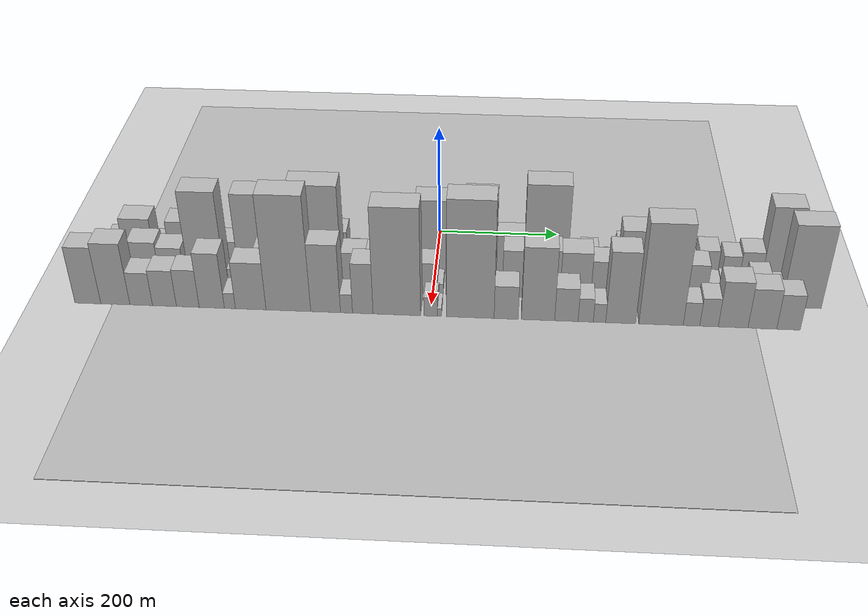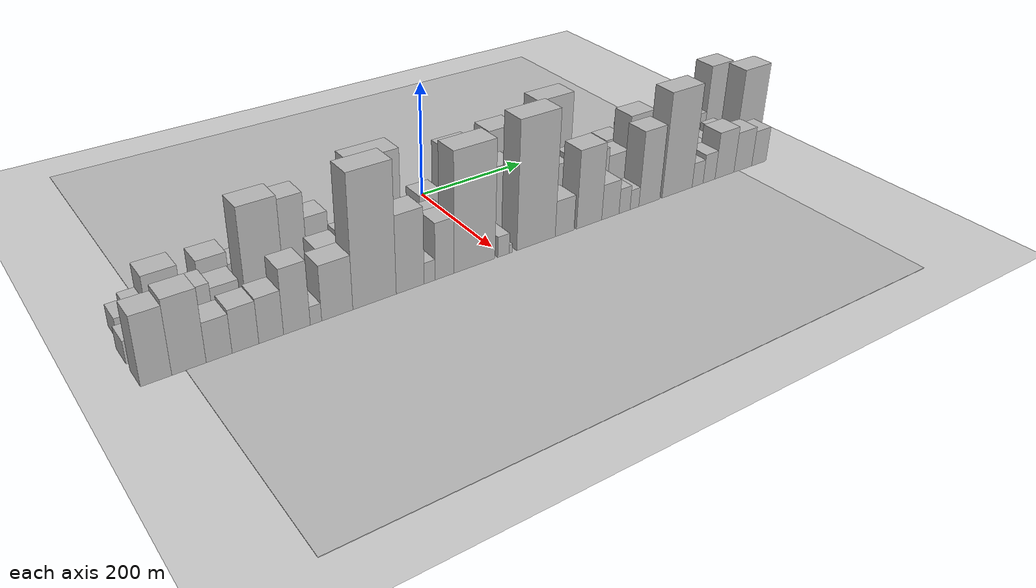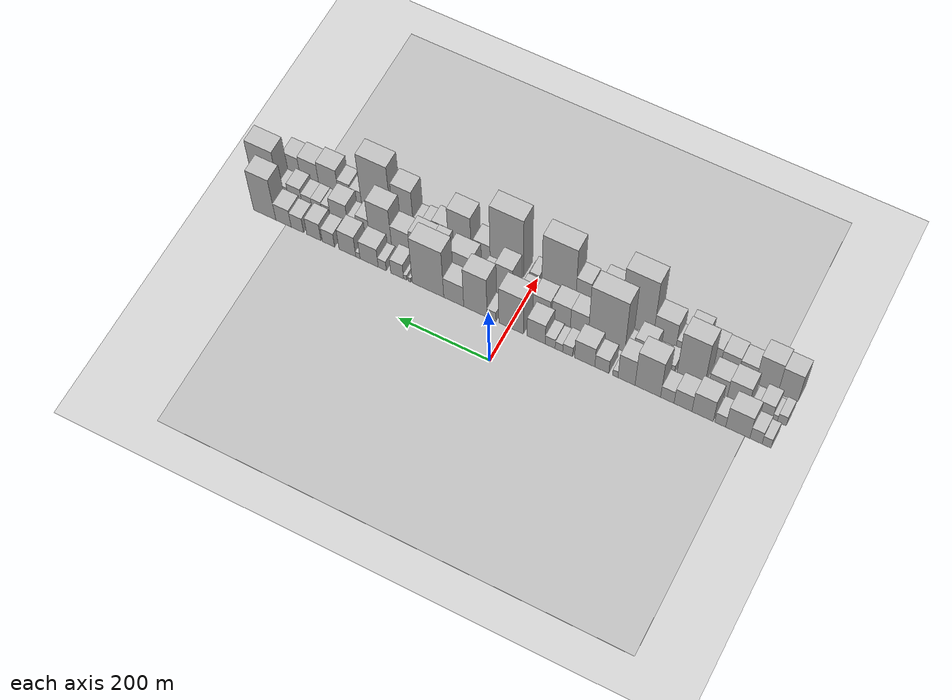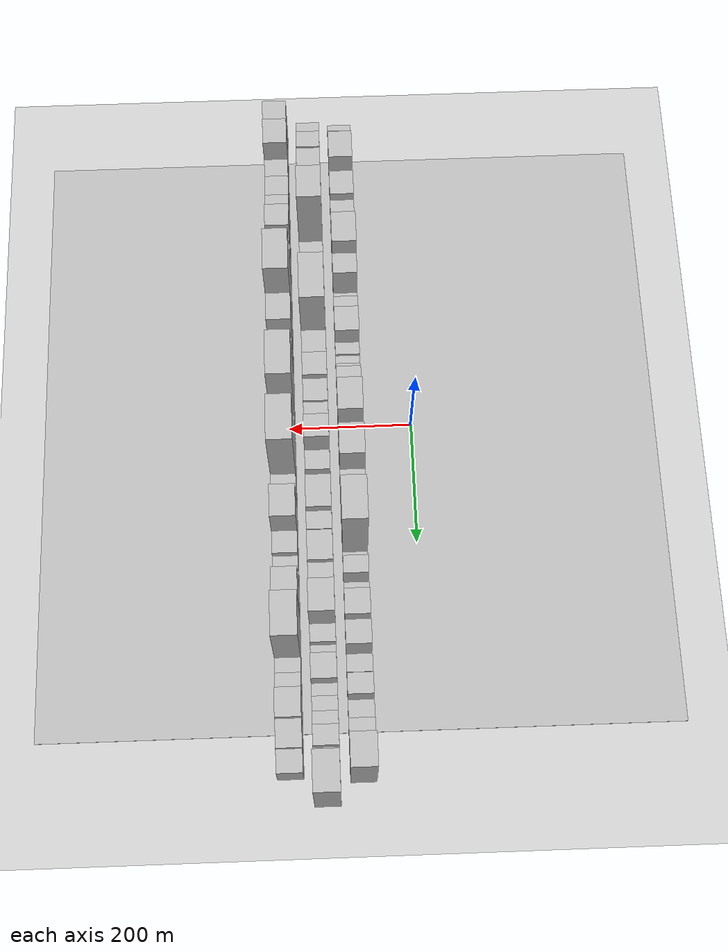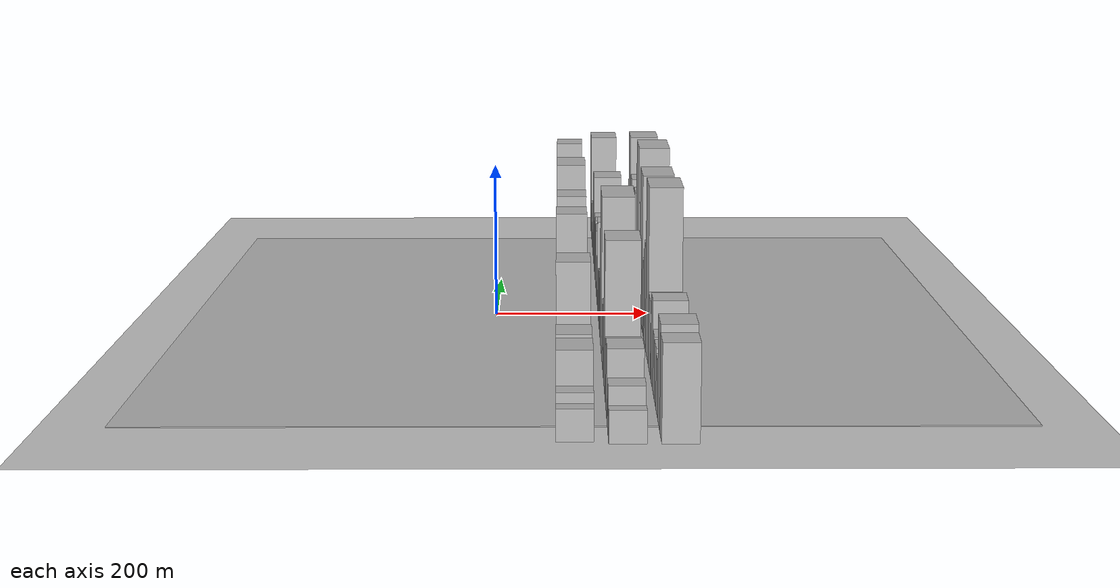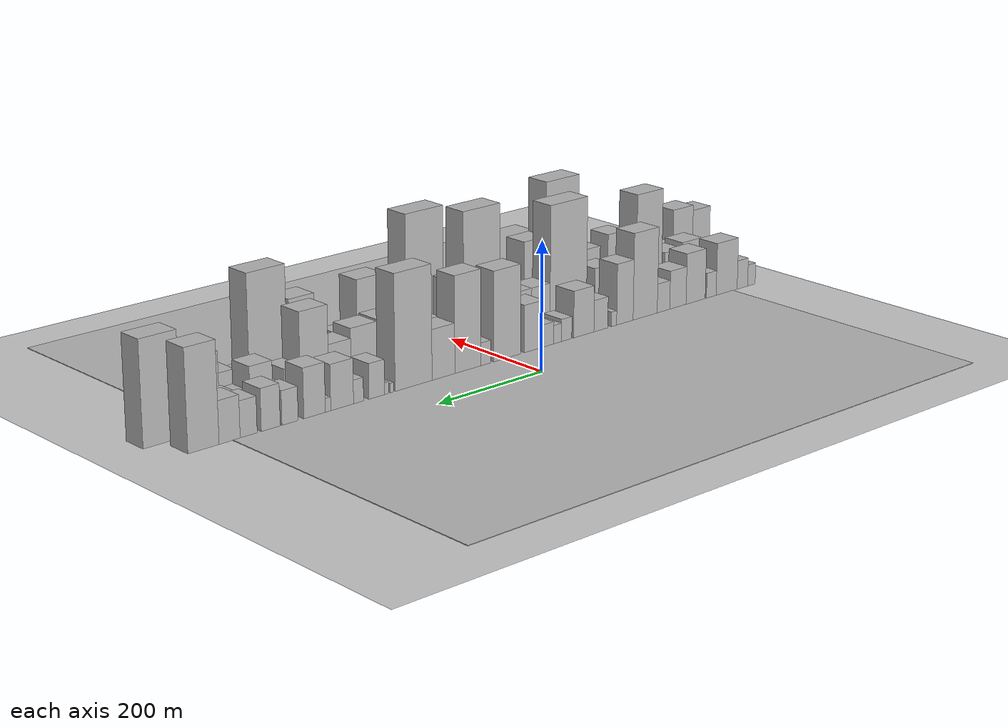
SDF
<?xml version="1.0" encoding="utf-8"?>

<sdf version="1.6">

   <world name="default">

      <gui fullscreen="0">

         <camera name="user_camera">

            <pose>-15 0 4.57585 0 0 0</pose>

            <view_controller>orbit</view_controller>

         </camera>

      </gui>

      <scene>

         <sky>

           <clouds>

             <speed>12</speed>

           </clouds>

         </sky>

         <ambient>0.4 0.4 0.4 1</ambient>

         <background>0.7 0.7 0.7 1</background>

         <shadows>1</shadows>

      </scene>

      <gravity>0 0 -9.8066</gravity>

      <magnetic_field>6e-06 2.3e-05 -4.2e-05</magnetic_field>

      <physics default="0" name="default_physics" type="ode">

         <ode>

            <solver>

               <type>quick</type>

               <iters>10</iters>

               <sor>1.0</sor>

               <use_dynamic_moi_rescaling>0</use_dynamic_moi_rescaling>

            </solver>

            <constraints>

               <cfm>0</cfm>

               <erp>0.2</erp>

               <contact_max_correcting_vel>100</contact_max_correcting_vel>

               <contact_surface_layer>0.001</contact_surface_layer>

            </constraints>

         </ode>

         <max_step_size>0.004</max_step_size>

         <real_time_factor>1</real_time_factor>

         <real_time_update_rate>250</real_time_update_rate>

      </physics>

      <light name="sun" type="directional">

         <cast_shadows>1</cast_shadows>

         <pose>0 0 10 0 0 0</pose>

         <diffuse>0.8 0.8 0.8 1</diffuse>

         <specular>0.2 0.2 0.2 1</specular>

         <attenuation>

            <range>1000</range>

            <constant>0.9</constant>

            <linear>0.01</linear>

            <quadratic>0.001</quadratic>

         </attenuation>

         <direction>-0.5 0.1 -0.9</direction>

      </light>

      <include>

         <name>ground_plane_1</name>

         <uri>model://HANNAS_ground_plane</uri>

         <pose>0 0 0  0 0 0</pose>

      </include>

      <include>

         <name>ground_plane_2</name>

         <uri>model://HANNAS_ground_plane</uri>

         <pose>100 0 0  0 0 0</pose>

      </include>

      <model name="building_1">

         <static>1</static>

         <pose frame="">100.0000 -543.7677 0 0.000000 0.000000 0.000000</pose>

         <link name="link">

            <pose frame="">0 0 18.00 0 0 0</pose>

            <collision name="collision">

               <geometry>

                  <box>

                     <size>40.0000 18.4647 36.0000</size>

                  </box>

               </geometry>

               <max_contacts>10</max_contacts>

               <surface>

                  <contact>

                     <ode/>

                  </contact>

                  <bounce/>

                  <friction>

                     <torsional>

                        <ode/>

                     </torsional>

                     <ode/>

                  </friction>

               </surface>

            </collision>

            <visual name="visual">

               <cast_shadows>0</cast_shadows>

               <geometry>

                  <box>

                     <size>40.0000 18.4647 36.0000</size>

                  </box>

               </geometry>

               <material>

                  <script>

                     <uri>model://HANNAS_wall/materials/scripts</uri>

                     <uri>model://HANNAS_wall/materials/textures</uri>

                     <name>vrc/HANNAS_wall</name>

                  </script>

               </material>

            </visual>

            <self_collide>0</self_collide>

            <enable_wind>0</enable_wind>

            <kinematic>0</kinematic>

         </link>

      </model>

      <model name="building_2">

         <static>1</static>

         <pose frame="">100.0000 -522.0372 0 0.000000 0.000000 0.000000</pose>

         <link name="link">

            <pose frame="">0 0 24.00 0 0 0</pose>

            <collision name="collision">

               <geometry>

                  <box>

                     <size>40.0000 24.9964 48.0000</size>

                  </box>

               </geometry>

               <max_contacts>10</max_contacts>

               <surface>

                  <contact>

                     <ode/>

                  </contact>

                  <bounce/>

                  <friction>

                     <torsional>

                        <ode/>

                     </torsional>

                     <ode/>

                  </friction>

               </surface>

            </collision>

            <visual name="visual">

               <cast_shadows>0</cast_shadows>

               <geometry>

                  <box>

                     <size>40.0000 24.9964 48.0000</size>

                  </box>

               </geometry>

               <material>

                  <script>

                     <uri>model://HANNAS_wall/materials/scripts</uri>

                     <uri>model://HANNAS_wall/materials/textures</uri>

                     <name>vrc/HANNAS_wall</name>

                  </script>

               </material>

            </visual>

            <self_collide>0</self_collide>

            <enable_wind>0</enable_wind>

            <kinematic>0</kinematic>

         </link>

      </model>

      <model name="building_3">

         <static>1</static>

         <pose frame="">100.0000 -484.5525 0 0.000000 0.000000 0.000000</pose>

         <link name="link">

            <pose frame="">0 0 43.50 0 0 0</pose>

            <collision name="collision">

               <geometry>

                  <box>

                     <size>40.0000 49.9729 87.0000</size>

                  </box>

               </geometry>

               <max_contacts>10</max_contacts>

               <surface>

                  <contact>

                     <ode/>

                  </contact>

                  <bounce/>

                  <friction>

                     <torsional>

                        <ode/>

                     </torsional>

                     <ode/>

                  </friction>

               </surface>

            </collision>

            <visual name="visual">

               <cast_shadows>0</cast_shadows>

               <geometry>

                  <box>

                     <size>40.0000 49.9729 87.0000</size>

                  </box>

               </geometry>

               <material>

                  <script>

                     <uri>model://HANNAS_wall/materials/scripts</uri>

                     <uri>model://HANNAS_wall/materials/textures</uri>

                     <name>vrc/HANNAS_wall</name>

                  </script>

               </material>

            </visual>

            <self_collide>0</self_collide>

            <enable_wind>0</enable_wind>

            <kinematic>0</kinematic>

         </link>

      </model>

      <model name="building_4">

         <static>1</static>

         <pose frame="">100.0000 -448.2868 0 0.000000 0.000000 0.000000</pose>

         <link name="link">

            <pose frame="">0 0 21.00 0 0 0</pose>

            <collision name="collision">

               <geometry>

                  <box>

                     <size>40.0000 22.5584 42.0000</size>

                  </box>

               </geometry>

               <max_contacts>10</max_contacts>

               <surface>

                  <contact>

                     <ode/>

                  </contact>

                  <bounce/>

                  <friction>

                     <torsional>

                        <ode/>

                     </torsional>

                     <ode/>

                  </friction>

               </surface>

            </collision>

            <visual name="visual">

               <cast_shadows>0</cast_shadows>

               <geometry>

                  <box>

                     <size>40.0000 22.5584 42.0000</size>

                  </box>

               </geometry>

               <material>

                  <script>

                     <uri>model://HANNAS_wall/materials/scripts</uri>

                     <uri>model://HANNAS_wall/materials/textures</uri>

                     <name>vrc/HANNAS_wall</name>

                  </script>

               </material>

            </visual>

            <self_collide>0</self_collide>

            <enable_wind>0</enable_wind>

            <kinematic>0</kinematic>

         </link>

      </model>

      <model name="building_5">

         <static>1</static>

         <pose frame="">100.0000 -411.7803 0 0.000000 0.000000 0.000000</pose>

         <link name="link">

            <pose frame="">0 0 42.00 0 0 0</pose>

            <collision name="collision">

               <geometry>

                  <box>

                     <size>40.0000 44.4546 84.0000</size>

                  </box>

               </geometry>

               <max_contacts>10</max_contacts>

               <surface>

                  <contact>

                     <ode/>

                  </contact>

                  <bounce/>

                  <friction>

                     <torsional>

                        <ode/>

                     </torsional>

                     <ode/>

                  </friction>

               </surface>

            </collision>

            <visual name="visual">

               <cast_shadows>0</cast_shadows>

               <geometry>

                  <box>

                     <size>40.0000 44.4546 84.0000</size>

                  </box>

               </geometry>

               <material>

                  <script>

                     <uri>model://HANNAS_wall/materials/scripts</uri>

                     <uri>model://HANNAS_wall/materials/textures</uri>

                     <name>vrc/HANNAS_wall</name>

                  </script>

               </material>

            </visual>

            <self_collide>0</self_collide>

            <enable_wind>0</enable_wind>

            <kinematic>0</kinematic>

         </link>

      </model>

      <model name="building_6">

         <static>1</static>

         <pose frame="">100.0000 -370.8900 0 0.000000 0.000000 0.000000</pose>

         <link name="link">

            <pose frame="">0 0 31.50 0 0 0</pose>

            <collision name="collision">

               <geometry>

                  <box>

                     <size>40.0000 37.3261 63.0000</size>

                  </box>

               </geometry>

               <max_contacts>10</max_contacts>

               <surface>

                  <contact>

                     <ode/>

                  </contact>

                  <bounce/>

                  <friction>

                     <torsional>

                        <ode/>

                     </torsional>

                     <ode/>

                  </friction>

               </surface>

            </collision>

            <visual name="visual">

               <cast_shadows>0</cast_shadows>

               <geometry>

                  <box>

                     <size>40.0000 37.3261 63.0000</size>

                  </box>

               </geometry>

               <material>

                  <script>

                     <uri>model://HANNAS_wall/materials/scripts</uri>

                     <uri>model://HANNAS_wall/materials/textures</uri>

                     <name>vrc/HANNAS_wall</name>

                  </script>

               </material>

            </visual>

            <self_collide>0</self_collide>

            <enable_wind>0</enable_wind>

            <kinematic>0</kinematic>

         </link>

      </model>

      <model name="building_7">

         <static>1</static>

         <pose frame="">100.0000 -338.0870 0 0.000000 0.000000 0.000000</pose>

         <link name="link">

            <pose frame="">0 0 24.00 0 0 0</pose>

            <collision name="collision">

               <geometry>

                  <box>

                     <size>40.0000 28.2799 48.0000</size>

                  </box>

               </geometry>

               <max_contacts>10</max_contacts>

               <surface>

                  <contact>

                     <ode/>

                  </contact>

                  <bounce/>

                  <friction>

                     <torsional>

                        <ode/>

                     </torsional>

                     <ode/>

                  </friction>

               </surface>

            </collision>

            <visual name="visual">

               <cast_shadows>0</cast_shadows>

               <geometry>

                  <box>

                     <size>40.0000 28.2799 48.0000</size>

                  </box>

               </geometry>

               <material>

                  <script>

                     <uri>model://HANNAS_wall/materials/scripts</uri>

                     <uri>model://HANNAS_wall/materials/textures</uri>

                     <name>vrc/HANNAS_wall</name>

                  </script>

               </material>

            </visual>

            <self_collide>0</self_collide>

            <enable_wind>0</enable_wind>

            <kinematic>0</kinematic>

         </link>

      </model>

      <model name="building_8">

         <static>1</static>

         <pose frame="">100.0000 -297.0090 0 0.000000 0.000000 0.000000</pose>

         <link name="link">

            <pose frame="">0 0 70.50 0 0 0</pose>

            <collision name="collision">

               <geometry>

                  <box>

                     <size>40.0000 53.8760 141.0000</size>

                  </box>

               </geometry>

               <max_contacts>10</max_contacts>

               <surface>

                  <contact>

                     <ode/>

                  </contact>

                  <bounce/>

                  <friction>

                     <torsional>

                        <ode/>

                     </torsional>

                     <ode/>

                  </friction>

               </surface>

            </collision>

            <visual name="visual">

               <cast_shadows>0</cast_shadows>

               <geometry>

                  <box>

                     <size>40.0000 53.8760 141.0000</size>

                  </box>

               </geometry>

               <material>

                  <script>

                     <uri>model://HANNAS_wall/materials/scripts</uri>

                     <uri>model://HANNAS_wall/materials/textures</uri>

                     <name>vrc/HANNAS_wall</name>

                  </script>

               </material>

            </visual>

            <self_collide>0</self_collide>

            <enable_wind>0</enable_wind>

            <kinematic>0</kinematic>

         </link>

      </model>

      <model name="building_9">

         <static>1</static>

         <pose frame="">100.0000 -251.9656 0 0.000000 0.000000 0.000000</pose>

         <link name="link">

            <pose frame="">0 0 49.50 0 0 0</pose>

            <collision name="collision">

               <geometry>

                  <box>

                     <size>40.0000 36.2107 99.0000</size>

                  </box>

               </geometry>

               <max_contacts>10</max_contacts>

               <surface>

                  <contact>

                     <ode/>

                  </contact>

                  <bounce/>

                  <friction>

                     <torsional>

                        <ode/>

                     </torsional>

                     <ode/>

                  </friction>

               </surface>

            </collision>

            <visual name="visual">

               <cast_shadows>0</cast_shadows>

               <geometry>

                  <box>

                     <size>40.0000 36.2107 99.0000</size>

                  </box>

               </geometry>

               <material>

                  <script>

                     <uri>model://HANNAS_wall/materials/scripts</uri>

                     <uri>model://HANNAS_wall/materials/textures</uri>

                     <name>vrc/HANNAS_wall</name>

                  </script>

               </material>

            </visual>

            <self_collide>0</self_collide>

            <enable_wind>0</enable_wind>

            <kinematic>0</kinematic>

         </link>

      </model>

      <model name="building_10">

         <static>1</static>

         <pose frame="">100.0000 -228.2909 0 0.000000 0.000000 0.000000</pose>

         <link name="link">

            <pose frame="">0 0 12.00 0 0 0</pose>

            <collision name="collision">

               <geometry>

                  <box>

                     <size>40.0000 11.1388 24.0000</size>

                  </box>

               </geometry>

               <max_contacts>10</max_contacts>

               <surface>

                  <contact>

                     <ode/>

                  </contact>

                  <bounce/>

                  <friction>

                     <torsional>

                        <ode/>

                     </torsional>

                     <ode/>

                  </friction>

               </surface>

            </collision>

            <visual name="visual">

               <cast_shadows>0</cast_shadows>

               <geometry>

                  <box>

                     <size>40.0000 11.1388 24.0000</size>

                  </box>

               </geometry>

               <material>

                  <script>

                     <uri>model://HANNAS_wall/materials/scripts</uri>

                     <uri>model://HANNAS_wall/materials/textures</uri>

                     <name>vrc/HANNAS_wall</name>

                  </script>

               </material>

            </visual>

            <self_collide>0</self_collide>

            <enable_wind>0</enable_wind>

            <kinematic>0</kinematic>

         </link>

      </model>

      <model name="building_11">

         <static>1</static>

         <pose frame="">100.0000 -199.6961 0 0.000000 0.000000 0.000000</pose>

         <link name="link">

            <pose frame="">0 0 25.50 0 0 0</pose>

            <collision name="collision">

               <geometry>

                  <box>

                     <size>40.0000 30.0507 51.0000</size>

                  </box>

               </geometry>

               <max_contacts>10</max_contacts>

               <surface>

                  <contact>

                     <ode/>

                  </contact>

                  <bounce/>

                  <friction>

                     <torsional>

                        <ode/>

                     </torsional>

                     <ode/>

                  </friction>

               </surface>

            </collision>

            <visual name="visual">

               <cast_shadows>0</cast_shadows>

               <geometry>

                  <box>

                     <size>40.0000 30.0507 51.0000</size>

                  </box>

               </geometry>

               <material>

                  <script>

                     <uri>model://HANNAS_wall/materials/scripts</uri>

                     <uri>model://HANNAS_wall/materials/textures</uri>

                     <name>vrc/HANNAS_wall</name>

                  </script>

               </material>

            </visual>

            <self_collide>0</self_collide>

            <enable_wind>0</enable_wind>

            <kinematic>0</kinematic>

         </link>

      </model>

      <model name="building_12">

         <static>1</static>

         <pose frame="">100.0000 -163.0340 0 0.000000 0.000000 0.000000</pose>

         <link name="link">

            <pose frame="">0 0 37.50 0 0 0</pose>

            <collision name="collision">

               <geometry>

                  <box>

                     <size>40.0000 43.2736 75.0000</size>

                  </box>

               </geometry>

               <max_contacts>10</max_contacts>

               <surface>

                  <contact>

                     <ode/>

                  </contact>

                  <bounce/>

                  <friction>

                     <torsional>

                        <ode/>

                     </torsional>

                     <ode/>

                  </friction>

               </surface>

            </collision>

            <visual name="visual">

               <cast_shadows>0</cast_shadows>

               <geometry>

                  <box>

                     <size>40.0000 43.2736 75.0000</size>

                  </box>

               </geometry>

               <material>

                  <script>

                     <uri>model://HANNAS_wall/materials/scripts</uri>

                     <uri>model://HANNAS_wall/materials/textures</uri>

                     <name>vrc/HANNAS_wall</name>

                  </script>

               </material>

            </visual>

            <self_collide>0</self_collide>

            <enable_wind>0</enable_wind>

            <kinematic>0</kinematic>

         </link>

      </model>

      <model name="building_13">

         <static>1</static>

         <pose frame="">100.0000 -126.6479 0 0.000000 0.000000 0.000000</pose>

         <link name="link">

            <pose frame="">0 0 18.00 0 0 0</pose>

            <collision name="collision">

               <geometry>

                  <box>

                     <size>40.0000 21.4987 36.0000</size>

                  </box>

               </geometry>

               <max_contacts>10</max_contacts>

               <surface>

                  <contact>

                     <ode/>

                  </contact>

                  <bounce/>

                  <friction>

                     <torsional>

                        <ode/>

                     </torsional>

                     <ode/>

                  </friction>

               </surface>

            </collision>

            <visual name="visual">

               <cast_shadows>0</cast_shadows>

               <geometry>

                  <box>

                     <size>40.0000 21.4987 36.0000</size>

                  </box>

               </geometry>

               <material>

                  <script>

                     <uri>model://HANNAS_wall/materials/scripts</uri>

                     <uri>model://HANNAS_wall/materials/textures</uri>

                     <name>vrc/HANNAS_wall</name>

                  </script>

               </material>

            </visual>

            <self_collide>0</self_collide>

            <enable_wind>0</enable_wind>

            <kinematic>0</kinematic>

         </link>

      </model>

      <model name="building_14">

         <static>1</static>

         <pose frame="">100.0000 -107.7903 0 0.000000 0.000000 0.000000</pose>

         <link name="link">

            <pose frame="">0 0 15.00 0 0 0</pose>

            <collision name="collision">

               <geometry>

                  <box>

                     <size>40.0000 16.2166 30.0000</size>

                  </box>

               </geometry>

               <max_contacts>10</max_contacts>

               <surface>

                  <contact>

                     <ode/>

                  </contact>

                  <bounce/>

                  <friction>

                     <torsional>

                        <ode/>

                     </torsional>

                     <ode/>

                  </friction>

               </surface>

            </collision>

            <visual name="visual">

               <cast_shadows>0</cast_shadows>

               <geometry>

                  <box>

                     <size>40.0000 16.2166 30.0000</size>

                  </box>

               </geometry>

               <material>

                  <script>

                     <uri>model://HANNAS_wall/materials/scripts</uri>

                     <uri>model://HANNAS_wall/materials/textures</uri>

                     <name>vrc/HANNAS_wall</name>

                  </script>

               </material>

            </visual>

            <self_collide>0</self_collide>

            <enable_wind>0</enable_wind>

            <kinematic>0</kinematic>

         </link>

      </model>

      <model name="building_15">

         <static>1</static>

         <pose frame="">100.0000 -88.9805 0 0.000000 0.000000 0.000000</pose>

         <link name="link">

            <pose frame="">0 0 18.00 0 0 0</pose>

            <collision name="collision">

               <geometry>

                  <box>

                     <size>40.0000 21.4029 36.0000</size>

                  </box>

               </geometry>

               <max_contacts>10</max_contacts>

               <surface>

                  <contact>

                     <ode/>

                  </contact>

                  <bounce/>

                  <friction>

                     <torsional>

                        <ode/>

                     </torsional>

                     <ode/>

                  </friction>

               </surface>

            </collision>

            <visual name="visual">

               <cast_shadows>0</cast_shadows>

               <geometry>

                  <box>

                     <size>40.0000 21.4029 36.0000</size>

                  </box>

               </geometry>

               <material>

                  <script>

                     <uri>model://HANNAS_wall/materials/scripts</uri>

                     <uri>model://HANNAS_wall/materials/textures</uri>

                     <name>vrc/HANNAS_wall</name>

                  </script>

               </material>

            </visual>

            <self_collide>0</self_collide>

            <enable_wind>0</enable_wind>

            <kinematic>0</kinematic>

         </link>

      </model>

      <model name="building_16">

         <static>1</static>

         <pose frame="">100.0000 -58.6805 0 0.000000 0.000000 0.000000</pose>

         <link name="link">

            <pose frame="">0 0 37.50 0 0 0</pose>

            <collision name="collision">

               <geometry>

                  <box>

                     <size>40.0000 39.1971 75.0000</size>

                  </box>

               </geometry>

               <max_contacts>10</max_contacts>

               <surface>

                  <contact>

                     <ode/>

                  </contact>

                  <bounce/>

                  <friction>

                     <torsional>

                        <ode/>

                     </torsional>

                     <ode/>

                  </friction>

               </surface>

            </collision>

            <visual name="visual">

               <cast_shadows>0</cast_shadows>

               <geometry>

                  <box>

                     <size>40.0000 39.1971 75.0000</size>

                  </box>

               </geometry>

               <material>

                  <script>

                     <uri>model://HANNAS_wall/materials/scripts</uri>

                     <uri>model://HANNAS_wall/materials/textures</uri>

                     <name>vrc/HANNAS_wall</name>

                  </script>

               </material>

            </visual>

            <self_collide>0</self_collide>

            <enable_wind>0</enable_wind>

            <kinematic>0</kinematic>

         </link>

      </model>

      <model name="building_17">

         <static>1</static>

         <pose frame="">100.0000 -4.2618 0 0.000000 0.000000 0.000000</pose>

         <link name="link">

            <pose frame="">0 0 70.50 0 0 0</pose>

            <collision name="collision">

               <geometry>

                  <box>

                     <size>40.0000 53.6403 141.0000</size>

                  </box>

               </geometry>

               <max_contacts>10</max_contacts>

               <surface>

                  <contact>

                     <ode/>

                  </contact>

                  <bounce/>

                  <friction>

                     <torsional>

                        <ode/>

                     </torsional>

                     <ode/>

                  </friction>

               </surface>

            </collision>

            <visual name="visual">

               <cast_shadows>0</cast_shadows>

               <geometry>

                  <box>

                     <size>40.0000 53.6403 141.0000</size>

                  </box>

               </geometry>

               <material>

                  <script>

                     <uri>model://HANNAS_wall/materials/scripts</uri>

                     <uri>model://HANNAS_wall/materials/textures</uri>

                     <name>vrc/HANNAS_wall</name>

                  </script>

               </material>

            </visual>

            <self_collide>0</self_collide>

            <enable_wind>0</enable_wind>

            <kinematic>0</kinematic>

         </link>

      </model>

      <model name="building_18">

         <static>1</static>

         <pose frame="">100.0000 38.4075 0 0.000000 0.000000 0.000000</pose>

         <link name="link">

            <pose frame="">0 0 18.00 0 0 0</pose>

            <collision name="collision">

               <geometry>

                  <box>

                     <size>40.0000 19.6983 36.0000</size>

                  </box>

               </geometry>

               <max_contacts>10</max_contacts>

               <surface>

                  <contact>

                     <ode/>

                  </contact>

                  <bounce/>

                  <friction>

                     <torsional>

                        <ode/>

                     </torsional>

                     <ode/>

                  </friction>

               </surface>

            </collision>

            <visual name="visual">

               <cast_shadows>0</cast_shadows>

               <geometry>

                  <box>

                     <size>40.0000 19.6983 36.0000</size>

                  </box>

               </geometry>

               <material>

                  <script>

                     <uri>model://HANNAS_wall/materials/scripts</uri>

                     <uri>model://HANNAS_wall/materials/textures</uri>

                     <name>vrc/HANNAS_wall</name>

                  </script>

               </material>

            </visual>

            <self_collide>0</self_collide>

            <enable_wind>0</enable_wind>

            <kinematic>0</kinematic>

         </link>

      </model>

      <model name="building_19">

         <static>1</static>

         <pose frame="">100.0000 73.9389 0 0.000000 0.000000 0.000000</pose>

         <link name="link">

            <pose frame="">0 0 75.00 0 0 0</pose>

            <collision name="collision">

               <geometry>

                  <box>

                     <size>40.0000 51.3646 150.0000</size>

                  </box>

               </geometry>

               <max_contacts>10</max_contacts>

               <surface>

                  <contact>

                     <ode/>

                  </contact>

                  <bounce/>

                  <friction>

                     <torsional>

                        <ode/>

                     </torsional>

                     <ode/>

                  </friction>

               </surface>

            </collision>

            <visual name="visual">

               <cast_shadows>0</cast_shadows>

               <geometry>

                  <box>

                     <size>40.0000 51.3646 150.0000</size>

                  </box>

               </geometry>

               <material>

                  <script>

                     <uri>model://HANNAS_wall/materials/scripts</uri>

                     <uri>model://HANNAS_wall/materials/textures</uri>

                     <name>vrc/HANNAS_wall</name>

                  </script>

               </material>

            </visual>

            <self_collide>0</self_collide>

            <enable_wind>0</enable_wind>

            <kinematic>0</kinematic>

         </link>

      </model>

      <model name="building_20">

         <static>1</static>

         <pose frame="">100.0000 121.5936 0 0.000000 0.000000 0.000000</pose>

         <link name="link">

            <pose frame="">0 0 39.00 0 0 0</pose>

            <collision name="collision">

               <geometry>

                  <box>

                     <size>40.0000 43.9448 78.0000</size>

                  </box>

               </geometry>

               <max_contacts>10</max_contacts>

               <surface>

                  <contact>

                     <ode/>

                  </contact>

                  <bounce/>

                  <friction>

                     <torsional>

                        <ode/>

                     </torsional>

                     <ode/>

                  </friction>

               </surface>

            </collision>

            <visual name="visual">

               <cast_shadows>0</cast_shadows>

               <geometry>

                  <box>

                     <size>40.0000 43.9448 78.0000</size>

                  </box>

               </geometry>

               <material>

                  <script>

                     <uri>model://HANNAS_wall/materials/scripts</uri>

                     <uri>model://HANNAS_wall/materials/textures</uri>

                     <name>vrc/HANNAS_wall</name>

                  </script>

               </material>

            </visual>

            <self_collide>0</self_collide>

            <enable_wind>0</enable_wind>

            <kinematic>0</kinematic>

         </link>

      </model>

      <model name="building_21">

         <static>1</static>

         <pose frame="">100.0000 178.5082 0 0.000000 0.000000 0.000000</pose>

         <link name="link">

            <pose frame="">0 0 88.50 0 0 0</pose>

            <collision name="collision">

               <geometry>

                  <box>

                     <size>40.0000 69.8843 177.0000</size>

                  </box>

               </geometry>

               <max_contacts>10</max_contacts>

               <surface>

                  <contact>

                     <ode/>

                  </contact>

                  <bounce/>

                  <friction>

                     <torsional>

                        <ode/>

                     </torsional>

                     <ode/>

                  </friction>

               </surface>

            </collision>

            <visual name="visual">

               <cast_shadows>0</cast_shadows>

               <geometry>

                  <box>

                     <size>40.0000 69.8843 177.0000</size>

                  </box>

               </geometry>

               <material>

                  <script>

                     <uri>model://HANNAS_wall/materials/scripts</uri>

                     <uri>model://HANNAS_wall/materials/textures</uri>

                     <name>vrc/HANNAS_wall</name>

                  </script>

               </material>

            </visual>

            <self_collide>0</self_collide>

            <enable_wind>0</enable_wind>

            <kinematic>0</kinematic>

         </link>

      </model>

      <model name="building_22">

         <static>1</static>

         <pose frame="">100.0000 219.5186 0 0.000000 0.000000 0.000000</pose>

         <link name="link">

            <pose frame="">0 0 7.50 0 0 0</pose>

            <collision name="collision">

               <geometry>

                  <box>

                     <size>40.0000 6.1366 15.0000</size>

                  </box>

               </geometry>

               <max_contacts>10</max_contacts>

               <surface>

                  <contact>

                     <ode/>

                  </contact>

                  <bounce/>

                  <friction>

                     <torsional>

                        <ode/>

                     </torsional>

                     <ode/>

                  </friction>

               </surface>

            </collision>

            <visual name="visual">

               <cast_shadows>0</cast_shadows>

               <geometry>

                  <box>

                     <size>40.0000 6.1366 15.0000</size>

                  </box>

               </geometry>

               <material>

                  <script>

                     <uri>model://HANNAS_wall/materials/scripts</uri>

                     <uri>model://HANNAS_wall/materials/textures</uri>

                     <name>vrc/HANNAS_wall</name>

                  </script>

               </material>

            </visual>

            <self_collide>0</self_collide>

            <enable_wind>0</enable_wind>

            <kinematic>0</kinematic>

         </link>

      </model>

      <model name="building_23">

         <static>1</static>

         <pose frame="">100.0000 229.3494 0 0.000000 0.000000 0.000000</pose>

         <link name="link">

            <pose frame="">0 0 9.00 0 0 0</pose>

            <collision name="collision">

               <geometry>

                  <box>

                     <size>40.0000 7.5250 18.0000</size>

                  </box>

               </geometry>

               <max_contacts>10</max_contacts>

               <surface>

                  <contact>

                     <ode/>

                  </contact>

                  <bounce/>

                  <friction>

                     <torsional>

                        <ode/>

                     </torsional>

                     <ode/>

                  </friction>

               </surface>

            </collision>

            <visual name="visual">

               <cast_shadows>0</cast_shadows>

               <geometry>

                  <box>

                     <size>40.0000 7.5250 18.0000</size>

                  </box>

               </geometry>

               <material>

                  <script>

                     <uri>model://HANNAS_wall/materials/scripts</uri>

                     <uri>model://HANNAS_wall/materials/textures</uri>

                     <name>vrc/HANNAS_wall</name>

                  </script>

               </material>

            </visual>

            <self_collide>0</self_collide>

            <enable_wind>0</enable_wind>

            <kinematic>0</kinematic>

         </link>

      </model>

      <model name="building_24">

         <static>1</static>

         <pose frame="">100.0000 247.4347 0 0.000000 0.000000 0.000000</pose>

         <link name="link">

            <pose frame="">0 0 27.00 0 0 0</pose>

            <collision name="collision">

               <geometry>

                  <box>

                     <size>40.0000 28.6455 54.0000</size>

                  </box>

               </geometry>

               <max_contacts>10</max_contacts>

               <surface>

                  <contact>

                     <ode/>

                  </contact>

                  <bounce/>

                  <friction>

                     <torsional>

                        <ode/>

                     </torsional>

                     <ode/>

                  </friction>

               </surface>

            </collision>

            <visual name="visual">

               <cast_shadows>0</cast_shadows>

               <geometry>

                  <box>

                     <size>40.0000 28.6455 54.0000</size>

                  </box>

               </geometry>

               <material>

                  <script>

                     <uri>model://HANNAS_wall/materials/scripts</uri>

                     <uri>model://HANNAS_wall/materials/textures</uri>

                     <name>vrc/HANNAS_wall</name>

                  </script>

               </material>

            </visual>

            <self_collide>0</self_collide>

            <enable_wind>0</enable_wind>

            <kinematic>0</kinematic>

         </link>

      </model>

      <model name="building_25">

         <static>1</static>

         <pose frame="">100.0000 280.8469 0 0.000000 0.000000 0.000000</pose>

         <link name="link">

            <pose frame="">0 0 18.00 0 0 0</pose>

            <collision name="collision">

               <geometry>

                  <box>

                     <size>40.0000 18.1789 36.0000</size>

                  </box>

               </geometry>

               <max_contacts>10</max_contacts>

               <surface>

                  <contact>

                     <ode/>

                  </contact>

                  <bounce/>

                  <friction>

                     <torsional>

                        <ode/>

                     </torsional>

                     <ode/>

                  </friction>

               </surface>

            </collision>

            <visual name="visual">

               <cast_shadows>0</cast_shadows>

               <geometry>

                  <box>

                     <size>40.0000 18.1789 36.0000</size>

                  </box>

               </geometry>

               <material>

                  <script>

                     <uri>model://HANNAS_wall/materials/scripts</uri>

                     <uri>model://HANNAS_wall/materials/textures</uri>

                     <name>vrc/HANNAS_wall</name>

                  </script>

               </material>

            </visual>

            <self_collide>0</self_collide>

            <enable_wind>0</enable_wind>

            <kinematic>0</kinematic>

         </link>

      </model>

      <model name="building_26">

         <static>1</static>

         <pose frame="">100.0000 310.4308 0 0.000000 0.000000 0.000000</pose>

         <link name="link">

            <pose frame="">0 0 34.50 0 0 0</pose>

            <collision name="collision">

               <geometry>

                  <box>

                     <size>40.0000 40.9889 69.0000</size>

                  </box>

               </geometry>

               <max_contacts>10</max_contacts>

               <surface>

                  <contact>

                     <ode/>

                  </contact>

                  <bounce/>

                  <friction>

                     <torsional>

                        <ode/>

                     </torsional>

                     <ode/>

                  </friction>

               </surface>

            </collision>

            <visual name="visual">

               <cast_shadows>0</cast_shadows>

               <geometry>

                  <box>

                     <size>40.0000 40.9889 69.0000</size>

                  </box>

               </geometry>

               <material>

                  <script>

                     <uri>model://HANNAS_wall/materials/scripts</uri>

                     <uri>model://HANNAS_wall/materials/textures</uri>

                     <name>vrc/HANNAS_wall</name>

                  </script>

               </material>

            </visual>

            <self_collide>0</self_collide>

            <enable_wind>0</enable_wind>

            <kinematic>0</kinematic>

         </link>

      </model>

      <model name="building_27">

         <static>1</static>

         <pose frame="">100.0000 335.7173 0 0.000000 0.000000 0.000000</pose>

         <link name="link">

            <pose frame="">0 0 10.50 0 0 0</pose>

            <collision name="collision">

               <geometry>

                  <box>

                     <size>40.0000 9.5842 21.0000</size>

                  </box>

               </geometry>

               <max_contacts>10</max_contacts>

               <surface>

                  <contact>

                     <ode/>

                  </contact>

                  <bounce/>

                  <friction>

                     <torsional>

                        <ode/>

                     </torsional>

                     <ode/>

                  </friction>

               </surface>

            </collision>

            <visual name="visual">

               <cast_shadows>0</cast_shadows>

               <geometry>

                  <box>

                     <size>40.0000 9.5842 21.0000</size>

                  </box>

               </geometry>

               <material>

                  <script>

                     <uri>model://HANNAS_wall/materials/scripts</uri>

                     <uri>model://HANNAS_wall/materials/textures</uri>

                     <name>vrc/HANNAS_wall</name>

                  </script>

               </material>

            </visual>

            <self_collide>0</self_collide>

            <enable_wind>0</enable_wind>

            <kinematic>0</kinematic>

         </link>

      </model>

      <model name="building_28">

         <static>1</static>

         <pose frame="">100.0000 359.5613 0 0.000000 0.000000 0.000000</pose>

         <link name="link">

            <pose frame="">0 0 37.50 0 0 0</pose>

            <collision name="collision">

               <geometry>

                  <box>

                     <size>40.0000 38.1038 75.0000</size>

                  </box>

               </geometry>

               <max_contacts>10</max_contacts>

               <surface>

                  <contact>

                     <ode/>

                  </contact>

                  <bounce/>

                  <friction>

                     <torsional>

                        <ode/>

                     </torsional>

                     <ode/>

                  </friction>

               </surface>

            </collision>

            <visual name="visual">

               <cast_shadows>0</cast_shadows>

               <geometry>

                  <box>

                     <size>40.0000 38.1038 75.0000</size>

                  </box>

               </geometry>

               <material>

                  <script>

                     <uri>model://HANNAS_wall/materials/scripts</uri>

                     <uri>model://HANNAS_wall/materials/textures</uri>

                     <name>vrc/HANNAS_wall</name>

                  </script>

               </material>

            </visual>

            <self_collide>0</self_collide>

            <enable_wind>0</enable_wind>

            <kinematic>0</kinematic>

         </link>

      </model>

      <model name="building_29">

         <static>1</static>

         <pose frame="">100.0000 402.6842 0 0.000000 0.000000 0.000000</pose>

         <link name="link">

            <pose frame="">0 0 25.50 0 0 0</pose>

            <collision name="collision">

               <geometry>

                  <box>

                     <size>40.0000 28.1420 51.0000</size>

                  </box>

               </geometry>

               <max_contacts>10</max_contacts>

               <surface>

                  <contact>

                     <ode/>

                  </contact>

                  <bounce/>

                  <friction>

                     <torsional>

                        <ode/>

                     </torsional>

                     <ode/>

                  </friction>

               </surface>

            </collision>

            <visual name="visual">

               <cast_shadows>0</cast_shadows>

               <geometry>

                  <box>

                     <size>40.0000 28.1420 51.0000</size>

                  </box>

               </geometry>

               <material>

                  <script>

                     <uri>model://HANNAS_wall/materials/scripts</uri>

                     <uri>model://HANNAS_wall/materials/textures</uri>

                     <name>vrc/HANNAS_wall</name>

                  </script>

               </material>

            </visual>

            <self_collide>0</self_collide>

            <enable_wind>0</enable_wind>

            <kinematic>0</kinematic>

         </link>

      </model>

      <model name="building_30">

         <static>1</static>

         <pose frame="">100.0000 436.0479 0 0.000000 0.000000 0.000000</pose>

         <link name="link">

            <pose frame="">0 0 31.50 0 0 0</pose>

            <collision name="collision">

               <geometry>

                  <box>

                     <size>40.0000 32.5853 63.0000</size>

                  </box>

               </geometry>

               <max_contacts>10</max_contacts>

               <surface>

                  <contact>

                     <ode/>

                  </contact>

                  <bounce/>

                  <friction>

                     <torsional>

                        <ode/>

                     </torsional>

                     <ode/>

                  </friction>

               </surface>

            </collision>

            <visual name="visual">

               <cast_shadows>0</cast_shadows>

               <geometry>

                  <box>

                     <size>40.0000 32.5853 63.0000</size>

                  </box>

               </geometry>

               <material>

                  <script>

                     <uri>model://HANNAS_wall/materials/scripts</uri>

                     <uri>model://HANNAS_wall/materials/textures</uri>

                     <name>vrc/HANNAS_wall</name>

                  </script>

               </material>

            </visual>

            <self_collide>0</self_collide>

            <enable_wind>0</enable_wind>

            <kinematic>0</kinematic>

         </link>

      </model>

      <model name="building_31">

         <static>1</static>

         <pose frame="">100.0000 473.7075 0 0.000000 0.000000 0.000000</pose>

         <link name="link">

            <pose frame="">0 0 27.00 0 0 0</pose>

            <collision name="collision">

               <geometry>

                  <box>

                     <size>40.0000 28.7339 54.0000</size>

                  </box>

               </geometry>

               <max_contacts>10</max_contacts>

               <surface>

                  <contact>

                     <ode/>

                  </contact>

                  <bounce/>

                  <friction>

                     <torsional>

                        <ode/>

                     </torsional>

                     <ode/>

                  </friction>

               </surface>

            </collision>

            <visual name="visual">

               <cast_shadows>0</cast_shadows>

               <geometry>

                  <box>

                     <size>40.0000 28.7339 54.0000</size>

                  </box>

               </geometry>

               <material>

                  <script>

                     <uri>model://HANNAS_wall/materials/scripts</uri>

                     <uri>model://HANNAS_wall/materials/textures</uri>

                     <name>vrc/HANNAS_wall</name>

                  </script>

               </material>

            </visual>

            <self_collide>0</self_collide>

            <enable_wind>0</enable_wind>

            <kinematic>0</kinematic>

         </link>

      </model>

      <model name="building_32">

         <static>1</static>

         <pose frame="">100.0000 505.7392 0 0.000000 0.000000 0.000000</pose>

         <link name="link">

            <pose frame="">0 0 31.50 0 0 0</pose>

            <collision name="collision">

               <geometry>

                  <box>

                     <size>40.0000 35.3296 63.0000</size>

                  </box>

               </geometry>

               <max_contacts>10</max_contacts>

               <surface>

                  <contact>

                     <ode/>

                  </contact>

                  <bounce/>

                  <friction>

                     <torsional>

                        <ode/>

                     </torsional>

                     <ode/>

                  </friction>

               </surface>

            </collision>

            <visual name="visual">

               <cast_shadows>0</cast_shadows>

               <geometry>

                  <box>

                     <size>40.0000 35.3296 63.0000</size>

                  </box>

               </geometry>

               <material>

                  <script>

                     <uri>model://HANNAS_wall/materials/scripts</uri>

                     <uri>model://HANNAS_wall/materials/textures</uri>

                     <name>vrc/HANNAS_wall</name>

                  </script>

               </material>

            </visual>

            <self_collide>0</self_collide>

            <enable_wind>0</enable_wind>

            <kinematic>0</kinematic>

         </link>

      </model>

      <model name="building_33">

         <static>1</static>

         <pose frame="">100.0000 549.0636 0 0.000000 0.000000 0.000000</pose>

         <link name="link">

            <pose frame="">0 0 75.00 0 0 0</pose>

            <collision name="collision">

               <geometry>

                  <box>

                     <size>40.0000 51.3193 150.0000</size>

                  </box>

               </geometry>

               <max_contacts>10</max_contacts>

               <surface>

                  <contact>

                     <ode/>

                  </contact>

                  <bounce/>

                  <friction>

                     <torsional>

                        <ode/>

                     </torsional>

                     <ode/>

                  </friction>

               </surface>

            </collision>

            <visual name="visual">

               <cast_shadows>0</cast_shadows>

               <geometry>

                  <box>

                     <size>40.0000 51.3193 150.0000</size>

                  </box>

               </geometry>

               <material>

                  <script>

                     <uri>model://HANNAS_wall/materials/scripts</uri>

                     <uri>model://HANNAS_wall/materials/textures</uri>

                     <name>vrc/HANNAS_wall</name>

                  </script>

               </material>

            </visual>

            <self_collide>0</self_collide>

            <enable_wind>0</enable_wind>

            <kinematic>0</kinematic>

         </link>

      </model>

      <model name="building_34">

         <static>1</static>

         <pose frame="">155.0000 -550.8006 0 0.000000 0.000000 0.000000</pose>

         <link name="link">

            <pose frame="">0 0 18.00 0 0 0</pose>

            <collision name="collision">

               <geometry>

                  <box>

                     <size>40.0000 18.3988 36.0000</size>

                  </box>

               </geometry>

               <max_contacts>10</max_contacts>

               <surface>

                  <contact>

                     <ode/>

                  </contact>

                  <bounce/>

                  <friction>

                     <torsional>

                        <ode/>

                     </torsional>

                     <ode/>

                  </friction>

               </surface>

            </collision>

            <visual name="visual">

               <cast_shadows>0</cast_shadows>

               <geometry>

                  <box>

                     <size>40.0000 18.3988 36.0000</size>

                  </box>

               </geometry>

               <material>

                  <script>

                     <uri>model://HANNAS_wall/materials/scripts</uri>

                     <uri>model://HANNAS_wall/materials/textures</uri>

                     <name>vrc/HANNAS_wall</name>

                  </script>

               </material>

            </visual>

            <self_collide>0</self_collide>

            <enable_wind>0</enable_wind>

            <kinematic>0</kinematic>

         </link>

      </model>

      <model name="building_35">

         <static>1</static>

         <pose frame="">155.0000 -536.6350 0 0.000000 0.000000 0.000000</pose>

         <link name="link">

            <pose frame="">0 0 12.00 0 0 0</pose>

            <collision name="collision">

               <geometry>

                  <box>

                     <size>40.0000 9.9324 24.0000</size>

                  </box>

               </geometry>

               <max_contacts>10</max_contacts>

               <surface>

                  <contact>

                     <ode/>

                  </contact>

                  <bounce/>

                  <friction>

                     <torsional>

                        <ode/>

                     </torsional>

                     <ode/>

                  </friction>

               </surface>

            </collision>

            <visual name="visual">

               <cast_shadows>0</cast_shadows>

               <geometry>

                  <box>

                     <size>40.0000 9.9324 24.0000</size>

                  </box>

               </geometry>

               <material>

                  <script>

                     <uri>model://HANNAS_wall/materials/scripts</uri>

                     <uri>model://HANNAS_wall/materials/textures</uri>

                     <name>vrc/HANNAS_wall</name>

                  </script>

               </material>

            </visual>

            <self_collide>0</self_collide>

            <enable_wind>0</enable_wind>

            <kinematic>0</kinematic>

         </link>

      </model>

      <model name="building_36">

         <static>1</static>

         <pose frame="">155.0000 -516.3487 0 0.000000 0.000000 0.000000</pose>

         <link name="link">

            <pose frame="">0 0 27.00 0 0 0</pose>

            <collision name="collision">

               <geometry>

                  <box>

                     <size>40.0000 30.6402 54.0000</size>

                  </box>

               </geometry>

               <max_contacts>10</max_contacts>

               <surface>

                  <contact>

                     <ode/>

                  </contact>

                  <bounce/>

                  <friction>

                     <torsional>

                        <ode/>

                     </torsional>

                     <ode/>

                  </friction>

               </surface>

            </collision>

            <visual name="visual">

               <cast_shadows>0</cast_shadows>

               <geometry>

                  <box>

                     <size>40.0000 30.6402 54.0000</size>

                  </box>

               </geometry>

               <material>

                  <script>

                     <uri>model://HANNAS_wall/materials/scripts</uri>

                     <uri>model://HANNAS_wall/materials/textures</uri>

                     <name>vrc/HANNAS_wall</name>

                  </script>

               </material>

            </visual>

            <self_collide>0</self_collide>

            <enable_wind>0</enable_wind>

            <kinematic>0</kinematic>

         </link>

      </model>

      <model name="building_37">

         <static>1</static>

         <pose frame="">155.0000 -493.0272 0 0.000000 0.000000 0.000000</pose>

         <link name="link">

            <pose frame="">0 0 15.00 0 0 0</pose>

            <collision name="collision">

               <geometry>

                  <box>

                     <size>40.0000 16.0028 30.0000</size>

                  </box>

               </geometry>

               <max_contacts>10</max_contacts>

               <surface>

                  <contact>

                     <ode/>

                  </contact>

                  <bounce/>

                  <friction>

                     <torsional>

                        <ode/>

                     </torsional>

                     <ode/>

                  </friction>

               </surface>

            </collision>

            <visual name="visual">

               <cast_shadows>0</cast_shadows>

               <geometry>

                  <box>

                     <size>40.0000 16.0028 30.0000</size>

                  </box>

               </geometry>

               <material>

                  <script>

                     <uri>model://HANNAS_wall/materials/scripts</uri>

                     <uri>model://HANNAS_wall/materials/textures</uri>

                     <name>vrc/HANNAS_wall</name>

                  </script>

               </material>

            </visual>

            <self_collide>0</self_collide>

            <enable_wind>0</enable_wind>

            <kinematic>0</kinematic>

         </link>

      </model>

      <model name="building_38">

         <static>1</static>

         <pose frame="">155.0000 -459.6206 0 0.000000 0.000000 0.000000</pose>

         <link name="link">

            <pose frame="">0 0 40.50 0 0 0</pose>

            <collision name="collision">

               <geometry>

                  <box>

                     <size>40.0000 44.8104 81.0000</size>

                  </box>

               </geometry>

               <max_contacts>10</max_contacts>

               <surface>

                  <contact>

                     <ode/>

                  </contact>

                  <bounce/>

                  <friction>

                     <torsional>

                        <ode/>

                     </torsional>

                     <ode/>

                  </friction>

               </surface>

            </collision>

            <visual name="visual">

               <cast_shadows>0</cast_shadows>

               <geometry>

                  <box>

                     <size>40.0000 44.8104 81.0000</size>

                  </box>

               </geometry>

               <material>

                  <script>

                     <uri>model://HANNAS_wall/materials/scripts</uri>

                     <uri>model://HANNAS_wall/materials/textures</uri>

                     <name>vrc/HANNAS_wall</name>

                  </script>

               </material>

            </visual>

            <self_collide>0</self_collide>

            <enable_wind>0</enable_wind>

            <kinematic>0</kinematic>

         </link>

      </model>

      <model name="building_39">

         <static>1</static>

         <pose frame="">155.0000 -417.0408 0 0.000000 0.000000 0.000000</pose>

         <link name="link">

            <pose frame="">0 0 36.00 0 0 0</pose>

            <collision name="collision">

               <geometry>

                  <box>

                     <size>40.0000 40.3492 72.0000</size>

                  </box>

               </geometry>

               <max_contacts>10</max_contacts>

               <surface>

                  <contact>

                     <ode/>

                  </contact>

                  <bounce/>

                  <friction>

                     <torsional>

                        <ode/>

                     </torsional>

                     <ode/>

                  </friction>

               </surface>

            </collision>

            <visual name="visual">

               <cast_shadows>0</cast_shadows>

               <geometry>

                  <box>

                     <size>40.0000 40.3492 72.0000</size>

                  </box>

               </geometry>

               <material>

                  <script>

                     <uri>model://HANNAS_wall/materials/scripts</uri>

                     <uri>model://HANNAS_wall/materials/textures</uri>

                     <name>vrc/HANNAS_wall</name>

                  </script>

               </material>

            </visual>

            <self_collide>0</self_collide>

            <enable_wind>0</enable_wind>

            <kinematic>0</kinematic>

         </link>

      </model>

      <model name="building_40">

         <static>1</static>

         <pose frame="">155.0000 -393.1645 0 0.000000 0.000000 0.000000</pose>

         <link name="link">

            <pose frame="">0 0 9.00 0 0 0</pose>

            <collision name="collision">

               <geometry>

                  <box>

                     <size>40.0000 7.4033 18.0000</size>

                  </box>

               </geometry>

               <max_contacts>10</max_contacts>

               <surface>

                  <contact>

                     <ode/>

                  </contact>

                  <bounce/>

                  <friction>

                     <torsional>

                        <ode/>

                     </torsional>

                     <ode/>

                  </friction>

               </surface>

            </collision>

            <visual name="visual">

               <cast_shadows>0</cast_shadows>

               <geometry>

                  <box>

                     <size>40.0000 7.4033 18.0000</size>

                  </box>

               </geometry>

               <material>

                  <script>

                     <uri>model://HANNAS_wall/materials/scripts</uri>

                     <uri>model://HANNAS_wall/materials/textures</uri>

                     <name>vrc/HANNAS_wall</name>

                  </script>

               </material>

            </visual>

            <self_collide>0</self_collide>

            <enable_wind>0</enable_wind>

            <kinematic>0</kinematic>

         </link>

      </model>

      <model name="building_41">

         <static>1</static>

         <pose frame="">155.0000 -360.5943 0 0.000000 0.000000 0.000000</pose>

         <link name="link">

            <pose frame="">0 0 90.00 0 0 0</pose>

            <collision name="collision">

               <geometry>

                  <box>

                     <size>40.0000 57.7371 180.0000</size>

                  </box>

               </geometry>

               <max_contacts>10</max_contacts>

               <surface>

                  <contact>

                     <ode/>

                  </contact>

                  <bounce/>

                  <friction>

                     <torsional>

                        <ode/>

                     </torsional>

                     <ode/>

                  </friction>

               </surface>

            </collision>

            <visual name="visual">

               <cast_shadows>0</cast_shadows>

               <geometry>

                  <box>

                     <size>40.0000 57.7371 180.0000</size>

                  </box>

               </geometry>

               <material>

                  <script>

                     <uri>model://HANNAS_wall/materials/scripts</uri>

                     <uri>model://HANNAS_wall/materials/textures</uri>

                     <name>vrc/HANNAS_wall</name>

                  </script>

               </material>

            </visual>

            <self_collide>0</self_collide>

            <enable_wind>0</enable_wind>

            <kinematic>0</kinematic>

         </link>

      </model>

      <model name="building_42">

         <static>1</static>

         <pose frame="">155.0000 -316.0157 0 0.000000 0.000000 0.000000</pose>

         <link name="link">

            <pose frame="">0 0 18.00 0 0 0</pose>

            <collision name="collision">

               <geometry>

                  <box>

                     <size>40.0000 21.4200 36.0000</size>

                  </box>

               </geometry>

               <max_contacts>10</max_contacts>

               <surface>

                  <contact>

                     <ode/>

                  </contact>

                  <bounce/>

                  <friction>

                     <torsional>

                        <ode/>

                     </torsional>

                     <ode/>

                  </friction>

               </surface>

            </collision>

            <visual name="visual">

               <cast_shadows>0</cast_shadows>

               <geometry>

                  <box>

                     <size>40.0000 21.4200 36.0000</size>

                  </box>

               </geometry>

               <material>

                  <script>

                     <uri>model://HANNAS_wall/materials/scripts</uri>

                     <uri>model://HANNAS_wall/materials/textures</uri>

                     <name>vrc/HANNAS_wall</name>

                  </script>

               </material>

            </visual>

            <self_collide>0</self_collide>

            <enable_wind>0</enable_wind>

            <kinematic>0</kinematic>

         </link>

      </model>

      <model name="building_43">

         <static>1</static>

         <pose frame="">155.0000 -291.9751 0 0.000000 0.000000 0.000000</pose>

         <link name="link">

            <pose frame="">0 0 13.50 0 0 0</pose>

            <collision name="collision">

               <geometry>

                  <box>

                     <size>40.0000 12.6612 27.0000</size>

                  </box>

               </geometry>

               <max_contacts>10</max_contacts>

               <surface>

                  <contact>

                     <ode/>

                  </contact>

                  <bounce/>

                  <friction>

                     <torsional>

                        <ode/>

                     </torsional>

                     <ode/>

                  </friction>

               </surface>

            </collision>

            <visual name="visual">

               <cast_shadows>0</cast_shadows>

               <geometry>

                  <box>

                     <size>40.0000 12.6612 27.0000</size>

                  </box>

               </geometry>

               <material>

                  <script>

                     <uri>model://HANNAS_wall/materials/scripts</uri>

                     <uri>model://HANNAS_wall/materials/textures</uri>

                     <name>vrc/HANNAS_wall</name>

                  </script>

               </material>

            </visual>

            <self_collide>0</self_collide>

            <enable_wind>0</enable_wind>

            <kinematic>0</kinematic>

         </link>

      </model>

      <model name="building_44">

         <static>1</static>

         <pose frame="">155.0000 -260.3991 0 0.000000 0.000000 0.000000</pose>

         <link name="link">

            <pose frame="">0 0 39.00 0 0 0</pose>

            <collision name="collision">

               <geometry>

                  <box>

                     <size>40.0000 40.4910 78.0000</size>

                  </box>

               </geometry>

               <max_contacts>10</max_contacts>

               <surface>

                  <contact>

                     <ode/>

                  </contact>

                  <bounce/>

                  <friction>

                     <torsional>

                        <ode/>

                     </torsional>

                     <ode/>

                  </friction>

               </surface>

            </collision>

            <visual name="visual">

               <cast_shadows>0</cast_shadows>

               <geometry>

                  <box>

                     <size>40.0000 40.4910 78.0000</size>

                  </box>

               </geometry>

               <material>

                  <script>

                     <uri>model://HANNAS_wall/materials/scripts</uri>

                     <uri>model://HANNAS_wall/materials/textures</uri>

                     <name>vrc/HANNAS_wall</name>

                  </script>

               </material>

            </visual>

            <self_collide>0</self_collide>

            <enable_wind>0</enable_wind>

            <kinematic>0</kinematic>

         </link>

      </model>

      <model name="building_45">

         <static>1</static>

         <pose frame="">155.0000 -228.0364 0 0.000000 0.000000 0.000000</pose>

         <link name="link">

            <pose frame="">0 0 13.50 0 0 0</pose>

            <collision name="collision">

               <geometry>

                  <box>

                     <size>40.0000 12.2343 27.0000</size>

                  </box>

               </geometry>

               <max_contacts>10</max_contacts>

               <surface>

                  <contact>

                     <ode/>

                  </contact>

                  <bounce/>

                  <friction>

                     <torsional>

                        <ode/>

                     </torsional>

                     <ode/>

                  </friction>

               </surface>

            </collision>

            <visual name="visual">

               <cast_shadows>0</cast_shadows>

               <geometry>

                  <box>

                     <size>40.0000 12.2343 27.0000</size>

                  </box>

               </geometry>

               <material>

                  <script>

                     <uri>model://HANNAS_wall/materials/scripts</uri>

                     <uri>model://HANNAS_wall/materials/textures</uri>

                     <name>vrc/HANNAS_wall</name>

                  </script>

               </material>

            </visual>

            <self_collide>0</self_collide>

            <enable_wind>0</enable_wind>

            <kinematic>0</kinematic>

         </link>

      </model>

      <model name="building_46">

         <static>1</static>

         <pose frame="">155.0000 -182.8427 0 0.000000 0.000000 0.000000</pose>

         <link name="link">

            <pose frame="">0 0 99.00 0 0 0</pose>

            <collision name="collision">

               <geometry>

                  <box>

                     <size>40.0000 78.1531 198.0000</size>

                  </box>

               </geometry>

               <max_contacts>10</max_contacts>

               <surface>

                  <contact>

                     <ode/>

                  </contact>

                  <bounce/>

                  <friction>

                     <torsional>

                        <ode/>

                     </torsional>

                     <ode/>

                  </friction>

               </surface>

            </collision>

            <visual name="visual">

               <cast_shadows>0</cast_shadows>

               <geometry>

                  <box>

                     <size>40.0000 78.1531 198.0000</size>

                  </box>

               </geometry>

               <material>

                  <script>

                     <uri>model://HANNAS_wall/materials/scripts</uri>

                     <uri>model://HANNAS_wall/materials/textures</uri>

                     <name>vrc/HANNAS_wall</name>

                  </script>

               </material>

            </visual>

            <self_collide>0</self_collide>

            <enable_wind>0</enable_wind>

            <kinematic>0</kinematic>

         </link>

      </model>

      <model name="building_47">

         <static>1</static>

         <pose frame="">155.0000 -124.4117 0 0.000000 0.000000 0.000000</pose>

         <link name="link">

            <pose frame="">0 0 37.50 0 0 0</pose>

            <collision name="collision">

               <geometry>

                  <box>

                     <size>40.0000 38.7090 75.0000</size>

                  </box>

               </geometry>

               <max_contacts>10</max_contacts>

               <surface>

                  <contact>

                     <ode/>

                  </contact>

                  <bounce/>

                  <friction>

                     <torsional>

                        <ode/>

                     </torsional>

                     <ode/>

                  </friction>

               </surface>

            </collision>

            <visual name="visual">

               <cast_shadows>0</cast_shadows>

               <geometry>

                  <box>

                     <size>40.0000 38.7090 75.0000</size>

                  </box>

               </geometry>

               <material>

                  <script>

                     <uri>model://HANNAS_wall/materials/scripts</uri>

                     <uri>model://HANNAS_wall/materials/textures</uri>

                     <name>vrc/HANNAS_wall</name>

                  </script>

               </material>

            </visual>

            <self_collide>0</self_collide>

            <enable_wind>0</enable_wind>

            <kinematic>0</kinematic>

         </link>

      </model>

      <model name="building_48">

         <static>1</static>

         <pose frame="">155.0000 -85.0469 0 0.000000 0.000000 0.000000</pose>

         <link name="link">

            <pose frame="">0 0 37.50 0 0 0</pose>

            <collision name="collision">

               <geometry>

                  <box>

                     <size>40.0000 40.0205 75.0000</size>

                  </box>

               </geometry>

               <max_contacts>10</max_contacts>

               <surface>

                  <contact>

                     <ode/>

                  </contact>

                  <bounce/>

                  <friction>

                     <torsional>

                        <ode/>

                     </torsional>

                     <ode/>

                  </friction>

               </surface>

            </collision>

            <visual name="visual">

               <cast_shadows>0</cast_shadows>

               <geometry>

                  <box>

                     <size>40.0000 40.0205 75.0000</size>

                  </box>

               </geometry>

               <material>

                  <script>

                     <uri>model://HANNAS_wall/materials/scripts</uri>

                     <uri>model://HANNAS_wall/materials/textures</uri>

                     <name>vrc/HANNAS_wall</name>

                  </script>

               </material>

            </visual>

            <self_collide>0</self_collide>

            <enable_wind>0</enable_wind>

            <kinematic>0</kinematic>

         </link>

      </model>

      <model name="building_49">

         <static>1</static>

         <pose frame="">155.0000 -42.5896 0 0.000000 0.000000 0.000000</pose>

         <link name="link">

            <pose frame="">0 0 33.00 0 0 0</pose>

            <collision name="collision">

               <geometry>

                  <box>

                     <size>40.0000 38.8941 66.0000</size>

                  </box>

               </geometry>

               <max_contacts>10</max_contacts>

               <surface>

                  <contact>

                     <ode/>

                  </contact>

                  <bounce/>

                  <friction>

                     <torsional>

                        <ode/>

                     </torsional>

                     <ode/>

                  </friction>

               </surface>

            </collision>

            <visual name="visual">

               <cast_shadows>0</cast_shadows>

               <geometry>

                  <box>

                     <size>40.0000 38.8941 66.0000</size>

                  </box>

               </geometry>

               <material>

                  <script>

                     <uri>model://HANNAS_wall/materials/scripts</uri>

                     <uri>model://HANNAS_wall/materials/textures</uri>

                     <name>vrc/HANNAS_wall</name>

                  </script>

               </material>

            </visual>

            <self_collide>0</self_collide>

            <enable_wind>0</enable_wind>

            <kinematic>0</kinematic>

         </link>

      </model>

      <model name="building_50">

         <static>1</static>

         <pose frame="">155.0000 -7.7787 0 0.000000 0.000000 0.000000</pose>

         <link name="link">

            <pose frame="">0 0 30.00 0 0 0</pose>

            <collision name="collision">

               <geometry>

                  <box>

                     <size>40.0000 30.7278 60.0000</size>

                  </box>

               </geometry>

               <max_contacts>10</max_contacts>

               <surface>

                  <contact>

                     <ode/>

                  </contact>

                  <bounce/>

                  <friction>

                     <torsional>

                        <ode/>

                     </torsional>

                     <ode/>

                  </friction>

               </surface>

            </collision>

            <visual name="visual">

               <cast_shadows>0</cast_shadows>

               <geometry>

                  <box>

                     <size>40.0000 30.7278 60.0000</size>

                  </box>

               </geometry>

               <material>

                  <script>

                     <uri>model://HANNAS_wall/materials/scripts</uri>

                     <uri>model://HANNAS_wall/materials/textures</uri>

                     <name>vrc/HANNAS_wall</name>

                  </script>

               </material>

            </visual>

            <self_collide>0</self_collide>

            <enable_wind>0</enable_wind>

            <kinematic>0</kinematic>

         </link>

      </model>

      <model name="building_51">

         <static>1</static>

         <pose frame="">155.0000 12.1256 0 0.000000 0.000000 0.000000</pose>

         <link name="link">

            <pose frame="">0 0 10.50 0 0 0</pose>

            <collision name="collision">

               <geometry>

                  <box>

                     <size>40.0000 9.0807 21.0000</size>

                  </box>

               </geometry>

               <max_contacts>10</max_contacts>

               <surface>

                  <contact>

                     <ode/>

                  </contact>

                  <bounce/>

                  <friction>

                     <torsional>

                        <ode/>

                     </torsional>

                     <ode/>

                  </friction>

               </surface>

            </collision>

            <visual name="visual">

               <cast_shadows>0</cast_shadows>

               <geometry>

                  <box>

                     <size>40.0000 9.0807 21.0000</size>

                  </box>

               </geometry>

               <material>

                  <script>

                     <uri>model://HANNAS_wall/materials/scripts</uri>

                     <uri>model://HANNAS_wall/materials/textures</uri>

                     <name>vrc/HANNAS_wall</name>

                  </script>

               </material>

            </visual>

            <self_collide>0</self_collide>

            <enable_wind>0</enable_wind>

            <kinematic>0</kinematic>

         </link>

      </model>

      <model name="building_52">

         <static>1</static>

         <pose frame="">155.0000 39.7600 0 0.000000 0.000000 0.000000</pose>

         <link name="link">

            <pose frame="">0 0 60.00 0 0 0</pose>

            <collision name="collision">

               <geometry>

                  <box>

                     <size>40.0000 38.1880 120.0000</size>

                  </box>

               </geometry>

               <max_contacts>10</max_contacts>

               <surface>

                  <contact>

                     <ode/>

                  </contact>

                  <bounce/>

                  <friction>

                     <torsional>

                        <ode/>

                     </torsional>

                     <ode/>

                  </friction>

               </surface>

            </collision>

            <visual name="visual">

               <cast_shadows>0</cast_shadows>

               <geometry>

                  <box>

                     <size>40.0000 38.1880 120.0000</size>

                  </box>

               </geometry>

               <material>

                  <script>

                     <uri>model://HANNAS_wall/materials/scripts</uri>

                     <uri>model://HANNAS_wall/materials/textures</uri>

                     <name>vrc/HANNAS_wall</name>

                  </script>

               </material>

            </visual>

            <self_collide>0</self_collide>

            <enable_wind>0</enable_wind>

            <kinematic>0</kinematic>

         </link>

      </model>

      <model name="building_53">

         <static>1</static>

         <pose frame="">155.0000 75.3585 0 0.000000 0.000000 0.000000</pose>

         <link name="link">

            <pose frame="">0 0 30.00 0 0 0</pose>

            <collision name="collision">

               <geometry>

                  <box>

                     <size>40.0000 33.0092 60.0000</size>

                  </box>

               </geometry>

               <max_contacts>10</max_contacts>

               <surface>

                  <contact>

                     <ode/>

                  </contact>

                  <bounce/>

                  <friction>

                     <torsional>

                        <ode/>

                     </torsional>

                     <ode/>

                  </friction>

               </surface>

            </collision>

            <visual name="visual">

               <cast_shadows>0</cast_shadows>

               <geometry>

                  <box>

                     <size>40.0000 33.0092 60.0000</size>

                  </box>

               </geometry>

               <material>

                  <script>

                     <uri>model://HANNAS_wall/materials/scripts</uri>

                     <uri>model://HANNAS_wall/materials/textures</uri>

                     <name>vrc/HANNAS_wall</name>

                  </script>

               </material>

            </visual>

            <self_collide>0</self_collide>

            <enable_wind>0</enable_wind>

            <kinematic>0</kinematic>

         </link>

      </model>

      <model name="building_54">

         <static>1</static>

         <pose frame="">155.0000 96.5791 0 0.000000 0.000000 0.000000</pose>

         <link name="link">

            <pose frame="">0 0 10.50 0 0 0</pose>

            <collision name="collision">

               <geometry>

                  <box>

                     <size>40.0000 9.4319 21.0000</size>

                  </box>

               </geometry>

               <max_contacts>10</max_contacts>

               <surface>

                  <contact>

                     <ode/>

                  </contact>

                  <bounce/>

                  <friction>

                     <torsional>

                        <ode/>

                     </torsional>

                     <ode/>

                  </friction>

               </surface>

            </collision>

            <visual name="visual">

               <cast_shadows>0</cast_shadows>

               <geometry>

                  <box>

                     <size>40.0000 9.4319 21.0000</size>

                  </box>

               </geometry>

               <material>

                  <script>

                     <uri>model://HANNAS_wall/materials/scripts</uri>

                     <uri>model://HANNAS_wall/materials/textures</uri>

                     <name>vrc/HANNAS_wall</name>

                  </script>

               </material>

            </visual>

            <self_collide>0</self_collide>

            <enable_wind>0</enable_wind>

            <kinematic>0</kinematic>

         </link>

      </model>

      <model name="building_55">

         <static>1</static>

         <pose frame="">155.0000 136.9483 0 0.000000 0.000000 0.000000</pose>

         <link name="link">

            <pose frame="">0 0 45.00 0 0 0</pose>

            <collision name="collision">

               <geometry>

                  <box>

                     <size>40.0000 53.3066 90.0000</size>

                  </box>

               </geometry>

               <max_contacts>10</max_contacts>

               <surface>

                  <contact>

                     <ode/>

                  </contact>

                  <bounce/>

                  <friction>

                     <torsional>

                        <ode/>

                     </torsional>

                     <ode/>

                  </friction>

               </surface>

            </collision>

            <visual name="visual">

               <cast_shadows>0</cast_shadows>

               <geometry>

                  <box>

                     <size>40.0000 53.3066 90.0000</size>

                  </box>

               </geometry>

               <material>

                  <script>

                     <uri>model://HANNAS_wall/materials/scripts</uri>

                     <uri>model://HANNAS_wall/materials/textures</uri>

                     <name>vrc/HANNAS_wall</name>

                  </script>

               </material>

            </visual>

            <self_collide>0</self_collide>

            <enable_wind>0</enable_wind>

            <kinematic>0</kinematic>

         </link>

      </model>

      <model name="building_56">

         <static>1</static>

         <pose frame="">155.0000 186.3522 0 0.000000 0.000000 0.000000</pose>

         <link name="link">

            <pose frame="">0 0 46.50 0 0 0</pose>

            <collision name="collision">

               <geometry>

                  <box>

                     <size>40.0000 29.5012 93.0000</size>

                  </box>

               </geometry>

               <max_contacts>10</max_contacts>

               <surface>

                  <contact>

                     <ode/>

                  </contact>

                  <bounce/>

                  <friction>

                     <torsional>

                        <ode/>

                     </torsional>

                     <ode/>

                  </friction>

               </surface>

            </collision>

            <visual name="visual">

               <cast_shadows>0</cast_shadows>

               <geometry>

                  <box>

                     <size>40.0000 29.5012 93.0000</size>

                  </box>

               </geometry>

               <material>

                  <script>

                     <uri>model://HANNAS_wall/materials/scripts</uri>

                     <uri>model://HANNAS_wall/materials/textures</uri>

                     <name>vrc/HANNAS_wall</name>

                  </script>

               </material>

            </visual>

            <self_collide>0</self_collide>

            <enable_wind>0</enable_wind>

            <kinematic>0</kinematic>

         </link>

      </model>

      <model name="building_57">

         <static>1</static>

         <pose frame="">155.0000 225.1708 0 0.000000 0.000000 0.000000</pose>

         <link name="link">

            <pose frame="">0 0 45.00 0 0 0</pose>

            <collision name="collision">

               <geometry>

                  <box>

                     <size>40.0000 48.1358 90.0000</size>

                  </box>

               </geometry>

               <max_contacts>10</max_contacts>

               <surface>

                  <contact>

                     <ode/>

                  </contact>

                  <bounce/>

                  <friction>

                     <torsional>

                        <ode/>

                     </torsional>

                     <ode/>

                  </friction>

               </surface>

            </collision>

            <visual name="visual">

               <cast_shadows>0</cast_shadows>

               <geometry>

                  <box>

                     <size>40.0000 48.1358 90.0000</size>

                  </box>

               </geometry>

               <material>

                  <script>

                     <uri>model://HANNAS_wall/materials/scripts</uri>

                     <uri>model://HANNAS_wall/materials/textures</uri>

                     <name>vrc/HANNAS_wall</name>

                  </script>

               </material>

            </visual>

            <self_collide>0</self_collide>

            <enable_wind>0</enable_wind>

            <kinematic>0</kinematic>

         </link>

      </model>

      <model name="building_58">

         <static>1</static>

         <pose frame="">155.0000 269.8080 0 0.000000 0.000000 0.000000</pose>

         <link name="link">

            <pose frame="">0 0 37.50 0 0 0</pose>

            <collision name="collision">

               <geometry>

                  <box>

                     <size>40.0000 41.1387 75.0000</size>

                  </box>

               </geometry>

               <max_contacts>10</max_contacts>

               <surface>

                  <contact>

                     <ode/>

                  </contact>

                  <bounce/>

                  <friction>

                     <torsional>

                        <ode/>

                     </torsional>

                     <ode/>

                  </friction>

               </surface>

            </collision>

            <visual name="visual">

               <cast_shadows>0</cast_shadows>

               <geometry>

                  <box>

                     <size>40.0000 41.1387 75.0000</size>

                  </box>

               </geometry>

               <material>

                  <script>

                     <uri>model://HANNAS_wall/materials/scripts</uri>

                     <uri>model://HANNAS_wall/materials/textures</uri>

                     <name>vrc/HANNAS_wall</name>

                  </script>

               </material>

            </visual>

            <self_collide>0</self_collide>

            <enable_wind>0</enable_wind>

            <kinematic>0</kinematic>

         </link>

      </model>

      <model name="building_59">

         <static>1</static>

         <pose frame="">155.0000 315.7709 0 0.000000 0.000000 0.000000</pose>

         <link name="link">

            <pose frame="">0 0 67.50 0 0 0</pose>

            <collision name="collision">

               <geometry>

                  <box>

                     <size>40.0000 50.7871 135.0000</size>

                  </box>

               </geometry>

               <max_contacts>10</max_contacts>

               <surface>

                  <contact>

                     <ode/>

                  </contact>

                  <bounce/>

                  <friction>

                     <torsional>

                        <ode/>

                     </torsional>

                     <ode/>

                  </friction>

               </surface>

            </collision>

            <visual name="visual">

               <cast_shadows>0</cast_shadows>

               <geometry>

                  <box>

                     <size>40.0000 50.7871 135.0000</size>

                  </box>

               </geometry>

               <material>

                  <script>

                     <uri>model://HANNAS_wall/materials/scripts</uri>

                     <uri>model://HANNAS_wall/materials/textures</uri>

                     <name>vrc/HANNAS_wall</name>

                  </script>

               </material>

            </visual>

            <self_collide>0</self_collide>

            <enable_wind>0</enable_wind>

            <kinematic>0</kinematic>

         </link>

      </model>

      <model name="building_60">

         <static>1</static>

         <pose frame="">155.0000 355.4239 0 0.000000 0.000000 0.000000</pose>

         <link name="link">

            <pose frame="">0 0 28.50 0 0 0</pose>

            <collision name="collision">

               <geometry>

                  <box>

                     <size>40.0000 28.5191 57.0000</size>

                  </box>

               </geometry>

               <max_contacts>10</max_contacts>

               <surface>

                  <contact>

                     <ode/>

                  </contact>

                  <bounce/>

                  <friction>

                     <torsional>

                        <ode/>

                     </torsional>

                     <ode/>

                  </friction>

               </surface>

            </collision>

            <visual name="visual">

               <cast_shadows>0</cast_shadows>

               <geometry>

                  <box>

                     <size>40.0000 28.5191 57.0000</size>

                  </box>

               </geometry>

               <material>

                  <script>

                     <uri>model://HANNAS_wall/materials/scripts</uri>

                     <uri>model://HANNAS_wall/materials/textures</uri>

                     <name>vrc/HANNAS_wall</name>

                  </script>

               </material>

            </visual>

            <self_collide>0</self_collide>

            <enable_wind>0</enable_wind>

            <kinematic>0</kinematic>

         </link>

      </model>

      <model name="building_61">

         <static>1</static>

         <pose frame="">155.0000 379.7930 0 0.000000 0.000000 0.000000</pose>

         <link name="link">

            <pose frame="">0 0 18.00 0 0 0</pose>

            <collision name="collision">

               <geometry>

                  <box>

                     <size>40.0000 20.2191 36.0000</size>

                  </box>

               </geometry>

               <max_contacts>10</max_contacts>

               <surface>

                  <contact>

                     <ode/>

                  </contact>

                  <bounce/>

                  <friction>

                     <torsional>

                        <ode/>

                     </torsional>

                     <ode/>

                  </friction>

               </surface>

            </collision>

            <visual name="visual">

               <cast_shadows>0</cast_shadows>

               <geometry>

                  <box>

                     <size>40.0000 20.2191 36.0000</size>

                  </box>

               </geometry>

               <material>

                  <script>

                     <uri>model://HANNAS_wall/materials/scripts</uri>

                     <uri>model://HANNAS_wall/materials/textures</uri>

                     <name>vrc/HANNAS_wall</name>

                  </script>

               </material>

            </visual>

            <self_collide>0</self_collide>

            <enable_wind>0</enable_wind>

            <kinematic>0</kinematic>

         </link>

      </model>

      <model name="building_62">

         <static>1</static>

         <pose frame="">155.0000 409.7057 0 0.000000 0.000000 0.000000</pose>

         <link name="link">

            <pose frame="">0 0 37.50 0 0 0</pose>

            <collision name="collision">

               <geometry>

                  <box>

                     <size>40.0000 39.6062 75.0000</size>

                  </box>

               </geometry>

               <max_contacts>10</max_contacts>

               <surface>

                  <contact>

                     <ode/>

                  </contact>

                  <bounce/>

                  <friction>

                     <torsional>

                        <ode/>

                     </torsional>

                     <ode/>

                  </friction>

               </surface>

            </collision>

            <visual name="visual">

               <cast_shadows>0</cast_shadows>

               <geometry>

                  <box>

                     <size>40.0000 39.6062 75.0000</size>

                  </box>

               </geometry>

               <material>

                  <script>

                     <uri>model://HANNAS_wall/materials/scripts</uri>

                     <uri>model://HANNAS_wall/materials/textures</uri>

                     <name>vrc/HANNAS_wall</name>

                  </script>

               </material>

            </visual>

            <self_collide>0</self_collide>

            <enable_wind>0</enable_wind>

            <kinematic>0</kinematic>

         </link>

      </model>

      <model name="building_63">

         <static>1</static>

         <pose frame="">155.0000 439.4043 0 0.000000 0.000000 0.000000</pose>

         <link name="link">

            <pose frame="">0 0 19.50 0 0 0</pose>

            <collision name="collision">

               <geometry>

                  <box>

                     <size>40.0000 19.7910 39.0000</size>

                  </box>

               </geometry>

               <max_contacts>10</max_contacts>

               <surface>

                  <contact>

                     <ode/>

                  </contact>

                  <bounce/>

                  <friction>

                     <torsional>

                        <ode/>

                     </torsional>

                     <ode/>

                  </friction>

               </surface>

            </collision>

            <visual name="visual">

               <cast_shadows>0</cast_shadows>

               <geometry>

                  <box>

                     <size>40.0000 19.7910 39.0000</size>

                  </box>

               </geometry>

               <material>

                  <script>

                     <uri>model://HANNAS_wall/materials/scripts</uri>

                     <uri>model://HANNAS_wall/materials/textures</uri>

                     <name>vrc/HANNAS_wall</name>

                  </script>

               </material>

            </visual>

            <self_collide>0</self_collide>

            <enable_wind>0</enable_wind>

            <kinematic>0</kinematic>

         </link>

      </model>

      <model name="building_64">

         <static>1</static>

         <pose frame="">155.0000 460.6255 0 0.000000 0.000000 0.000000</pose>

         <link name="link">

            <pose frame="">0 0 21.00 0 0 0</pose>

            <collision name="collision">

               <geometry>

                  <box>

                     <size>40.0000 22.6514 42.0000</size>

                  </box>

               </geometry>

               <max_contacts>10</max_contacts>

               <surface>

                  <contact>

                     <ode/>

                  </contact>

                  <bounce/>

                  <friction>

                     <torsional>

                        <ode/>

                     </torsional>

                     <ode/>

                  </friction>

               </surface>

            </collision>

            <visual name="visual">

               <cast_shadows>0</cast_shadows>

               <geometry>

                  <box>

                     <size>40.0000 22.6514 42.0000</size>

                  </box>

               </geometry>

               <material>

                  <script>

                     <uri>model://HANNAS_wall/materials/scripts</uri>

                     <uri>model://HANNAS_wall/materials/textures</uri>

                     <name>vrc/HANNAS_wall</name>

                  </script>

               </material>

            </visual>

            <self_collide>0</self_collide>

            <enable_wind>0</enable_wind>

            <kinematic>0</kinematic>

         </link>

      </model>

      <model name="building_65">

         <static>1</static>

         <pose frame="">155.0000 483.3495 0 0.000000 0.000000 0.000000</pose>

         <link name="link">

            <pose frame="">0 0 21.00 0 0 0</pose>

            <collision name="collision">

               <geometry>

                  <box>

                     <size>40.0000 22.7964 42.0000</size>

                  </box>

               </geometry>

               <max_contacts>10</max_contacts>

               <surface>

                  <contact>

                     <ode/>

                  </contact>

                  <bounce/>

                  <friction>

                     <torsional>

                        <ode/>

                     </torsional>

                     <ode/>

                  </friction>

               </surface>

            </collision>

            <visual name="visual">

               <cast_shadows>0</cast_shadows>

               <geometry>

                  <box>

                     <size>40.0000 22.7964 42.0000</size>

                  </box>

               </geometry>

               <material>

                  <script>

                     <uri>model://HANNAS_wall/materials/scripts</uri>

                     <uri>model://HANNAS_wall/materials/textures</uri>

                     <name>vrc/HANNAS_wall</name>

                  </script>

               </material>

            </visual>

            <self_collide>0</self_collide>

            <enable_wind>0</enable_wind>

            <kinematic>0</kinematic>

         </link>

      </model>

      <model name="building_66">

         <static>1</static>

         <pose frame="">155.0000 510.5578 0 0.000000 0.000000 0.000000</pose>

         <link name="link">

            <pose frame="">0 0 28.50 0 0 0</pose>

            <collision name="collision">

               <geometry>

                  <box>

                     <size>40.0000 31.6202 57.0000</size>

                  </box>

               </geometry>

               <max_contacts>10</max_contacts>

               <surface>

                  <contact>

                     <ode/>

                  </contact>

                  <bounce/>

                  <friction>

                     <torsional>

                        <ode/>

                     </torsional>

                     <ode/>

                  </friction>

               </surface>

            </collision>

            <visual name="visual">

               <cast_shadows>0</cast_shadows>

               <geometry>

                  <box>

                     <size>40.0000 31.6202 57.0000</size>

                  </box>

               </geometry>

               <material>

                  <script>

                     <uri>model://HANNAS_wall/materials/scripts</uri>

                     <uri>model://HANNAS_wall/materials/textures</uri>

                     <name>vrc/HANNAS_wall</name>

                  </script>

               </material>

            </visual>

            <self_collide>0</self_collide>

            <enable_wind>0</enable_wind>

            <kinematic>0</kinematic>

         </link>

      </model>

      <model name="building_67">

         <static>1</static>

         <pose frame="">155.0000 536.8856 0 0.000000 0.000000 0.000000</pose>

         <link name="link">

            <pose frame="">0 0 19.50 0 0 0</pose>

            <collision name="collision">

               <geometry>

                  <box>

                     <size>40.0000 21.0354 39.0000</size>

                  </box>

               </geometry>

               <max_contacts>10</max_contacts>

               <surface>

                  <contact>

                     <ode/>

                  </contact>

                  <bounce/>

                  <friction>

                     <torsional>

                        <ode/>

                     </torsional>

                     <ode/>

                  </friction>

               </surface>

            </collision>

            <visual name="visual">

               <cast_shadows>0</cast_shadows>

               <geometry>

                  <box>

                     <size>40.0000 21.0354 39.0000</size>

                  </box>

               </geometry>

               <material>

                  <script>

                     <uri>model://HANNAS_wall/materials/scripts</uri>

                     <uri>model://HANNAS_wall/materials/textures</uri>

                     <name>vrc/HANNAS_wall</name>

                  </script>

               </material>

            </visual>

            <self_collide>0</self_collide>

            <enable_wind>0</enable_wind>

            <kinematic>0</kinematic>

         </link>

      </model>

      <model name="building_68">

         <static>1</static>

         <pose frame="">155.0000 578.1728 0 0.000000 0.000000 0.000000</pose>

         <link name="link">

            <pose frame="">0 0 78.00 0 0 0</pose>

            <collision name="collision">

               <geometry>

                  <box>

                     <size>40.0000 61.5389 156.0000</size>

                  </box>

               </geometry>

               <max_contacts>10</max_contacts>

               <surface>

                  <contact>

                     <ode/>

                  </contact>

                  <bounce/>

                  <friction>

                     <torsional>

                        <ode/>

                     </torsional>

                     <ode/>

                  </friction>

               </surface>

            </collision>

            <visual name="visual">

               <cast_shadows>0</cast_shadows>

               <geometry>

                  <box>

                     <size>40.0000 61.5389 156.0000</size>

                  </box>

               </geometry>

               <material>

                  <script>

                     <uri>model://HANNAS_wall/materials/scripts</uri>

                     <uri>model://HANNAS_wall/materials/textures</uri>

                     <name>vrc/HANNAS_wall</name>

                  </script>

               </material>

            </visual>

            <self_collide>0</self_collide>

            <enable_wind>0</enable_wind>

            <kinematic>0</kinematic>

         </link>

      </model>

      <model name="building_69">

         <static>1</static>

         <pose frame="">210.0000 -539.4022 0 0.000000 0.000000 0.000000</pose>

         <link name="link">

            <pose frame="">0 0 54.00 0 0 0</pose>

            <collision name="collision">

               <geometry>

                  <box>

                     <size>40.0000 41.1955 108.0000</size>

                  </box>

               </geometry>

               <max_contacts>10</max_contacts>

               <surface>

                  <contact>

                     <ode/>

                  </contact>

                  <bounce/>

                  <friction>

                     <torsional>

                        <ode/>

                     </torsional>

                     <ode/>

                  </friction>

               </surface>

            </collision>

            <visual name="visual">

               <cast_shadows>0</cast_shadows>

               <geometry>

                  <box>

                     <size>40.0000 41.1955 108.0000</size>

                  </box>

               </geometry>

               <material>

                  <script>

                     <uri>model://HANNAS_wall/materials/scripts</uri>

                     <uri>model://HANNAS_wall/materials/textures</uri>

                     <name>vrc/HANNAS_wall</name>

                  </script>

               </material>

            </visual>

            <self_collide>0</self_collide>

            <enable_wind>0</enable_wind>

            <kinematic>0</kinematic>

         </link>

      </model>

      <model name="building_70">

         <static>1</static>

         <pose frame="">210.0000 -495.5633 0 0.000000 0.000000 0.000000</pose>

         <link name="link">

            <pose frame="">0 0 58.50 0 0 0</pose>

            <collision name="collision">

               <geometry>

                  <box>

                     <size>40.0000 46.4823 117.0000</size>

                  </box>

               </geometry>

               <max_contacts>10</max_contacts>

               <surface>

                  <contact>

                     <ode/>

                  </contact>

                  <bounce/>

                  <friction>

                     <torsional>

                        <ode/>

                     </torsional>

                     <ode/>

                  </friction>

               </surface>

            </collision>

            <visual name="visual">

               <cast_shadows>0</cast_shadows>

               <geometry>

                  <box>

                     <size>40.0000 46.4823 117.0000</size>

                  </box>

               </geometry>

               <material>

                  <script>

                     <uri>model://HANNAS_wall/materials/scripts</uri>

                     <uri>model://HANNAS_wall/materials/textures</uri>

                     <name>vrc/HANNAS_wall</name>

                  </script>

               </material>

            </visual>

            <self_collide>0</self_collide>

            <enable_wind>0</enable_wind>

            <kinematic>0</kinematic>

         </link>

      </model>

      <model name="building_71">

         <static>1</static>

         <pose frame="">210.0000 -454.3490 0 0.000000 0.000000 0.000000</pose>

         <link name="link">

            <pose frame="">0 0 31.50 0 0 0</pose>

            <collision name="collision">

               <geometry>

                  <box>

                     <size>40.0000 35.9462 63.0000</size>

                  </box>

               </geometry>

               <max_contacts>10</max_contacts>

               <surface>

                  <contact>

                     <ode/>

                  </contact>

                  <bounce/>

                  <friction>

                     <torsional>

                        <ode/>

                     </torsional>

                     <ode/>

                  </friction>

               </surface>

            </collision>

            <visual name="visual">

               <cast_shadows>0</cast_shadows>

               <geometry>

                  <box>

                     <size>40.0000 35.9462 63.0000</size>

                  </box>

               </geometry>

               <material>

                  <script>

                     <uri>model://HANNAS_wall/materials/scripts</uri>

                     <uri>model://HANNAS_wall/materials/textures</uri>

                     <name>vrc/HANNAS_wall</name>

                  </script>

               </material>

            </visual>

            <self_collide>0</self_collide>

            <enable_wind>0</enable_wind>

            <kinematic>0</kinematic>

         </link>

      </model>

      <model name="building_72">

         <static>1</static>

         <pose frame="">210.0000 -417.3780 0 0.000000 0.000000 0.000000</pose>

         <link name="link">

            <pose frame="">0 0 34.50 0 0 0</pose>

            <collision name="collision">

               <geometry>

                  <box>

                     <size>40.0000 37.9959 69.0000</size>

                  </box>

               </geometry>

               <max_contacts>10</max_contacts>

               <surface>

                  <contact>

                     <ode/>

                  </contact>

                  <bounce/>

                  <friction>

                     <torsional>

                        <ode/>

                     </torsional>

                     <ode/>

                  </friction>

               </surface>

            </collision>

            <visual name="visual">

               <cast_shadows>0</cast_shadows>

               <geometry>

                  <box>

                     <size>40.0000 37.9959 69.0000</size>

                  </box>

               </geometry>

               <material>

                  <script>

                     <uri>model://HANNAS_wall/materials/scripts</uri>

                     <uri>model://HANNAS_wall/materials/textures</uri>

                     <name>vrc/HANNAS_wall</name>

                  </script>

               </material>

            </visual>

            <self_collide>0</self_collide>

            <enable_wind>0</enable_wind>

            <kinematic>0</kinematic>

         </link>

      </model>

      <model name="building_73">

         <static>1</static>

         <pose frame="">210.0000 -380.3522 0 0.000000 0.000000 0.000000</pose>

         <link name="link">

            <pose frame="">0 0 36.00 0 0 0</pose>

            <collision name="collision">

               <geometry>

                  <box>

                     <size>40.0000 36.0558 72.0000</size>

                  </box>

               </geometry>

               <max_contacts>10</max_contacts>

               <surface>

                  <contact>

                     <ode/>

                  </contact>

                  <bounce/>

                  <friction>

                     <torsional>

                        <ode/>

                     </torsional>

                     <ode/>

                  </friction>

               </surface>

            </collision>

            <visual name="visual">

               <cast_shadows>0</cast_shadows>

               <geometry>

                  <box>

                     <size>40.0000 36.0558 72.0000</size>

                  </box>

               </geometry>

               <material>

                  <script>

                     <uri>model://HANNAS_wall/materials/scripts</uri>

                     <uri>model://HANNAS_wall/materials/textures</uri>

                     <name>vrc/HANNAS_wall</name>

                  </script>

               </material>

            </visual>

            <self_collide>0</self_collide>

            <enable_wind>0</enable_wind>

            <kinematic>0</kinematic>

         </link>

      </model>

      <model name="building_74">

         <static>1</static>

         <pose frame="">210.0000 -342.4402 0 0.000000 0.000000 0.000000</pose>

         <link name="link">

            <pose frame="">0 0 52.50 0 0 0</pose>

            <collision name="collision">

               <geometry>

                  <box>

                     <size>40.0000 39.7682 105.0000</size>

                  </box>

               </geometry>

               <max_contacts>10</max_contacts>

               <surface>

                  <contact>

                     <ode/>

                  </contact>

                  <bounce/>

                  <friction>

                     <torsional>

                        <ode/>

                     </torsional>

                     <ode/>

                  </friction>

               </surface>

            </collision>

            <visual name="visual">

               <cast_shadows>0</cast_shadows>

               <geometry>

                  <box>

                     <size>40.0000 39.7682 105.0000</size>

                  </box>

               </geometry>

               <material>

                  <script>

                     <uri>model://HANNAS_wall/materials/scripts</uri>

                     <uri>model://HANNAS_wall/materials/textures</uri>

                     <name>vrc/HANNAS_wall</name>

                  </script>

               </material>

            </visual>

            <self_collide>0</self_collide>

            <enable_wind>0</enable_wind>

            <kinematic>0</kinematic>

         </link>

      </model>

      <model name="building_75">

         <static>1</static>

         <pose frame="">210.0000 -313.8817 0 0.000000 0.000000 0.000000</pose>

         <link name="link">

            <pose frame="">0 0 15.00 0 0 0</pose>

            <collision name="collision">

               <geometry>

                  <box>

                     <size>40.0000 17.3487 30.0000</size>

                  </box>

               </geometry>

               <max_contacts>10</max_contacts>

               <surface>

                  <contact>

                     <ode/>

                  </contact>

                  <bounce/>

                  <friction>

                     <torsional>

                        <ode/>

                     </torsional>

                     <ode/>

                  </friction>

               </surface>

            </collision>

            <visual name="visual">

               <cast_shadows>0</cast_shadows>

               <geometry>

                  <box>

                     <size>40.0000 17.3487 30.0000</size>

                  </box>

               </geometry>

               <material>

                  <script>

                     <uri>model://HANNAS_wall/materials/scripts</uri>

                     <uri>model://HANNAS_wall/materials/textures</uri>

                     <name>vrc/HANNAS_wall</name>

                  </script>

               </material>

            </visual>

            <self_collide>0</self_collide>

            <enable_wind>0</enable_wind>

            <kinematic>0</kinematic>

         </link>

      </model>

      <model name="building_76">

         <static>1</static>

         <pose frame="">210.0000 -280.9880 0 0.000000 0.000000 0.000000</pose>

         <link name="link">

            <pose frame="">0 0 45.00 0 0 0</pose>

            <collision name="collision">

               <geometry>

                  <box>

                     <size>40.0000 48.4388 90.0000</size>

                  </box>

               </geometry>

               <max_contacts>10</max_contacts>

               <surface>

                  <contact>

                     <ode/>

                  </contact>

                  <bounce/>

                  <friction>

                     <torsional>

                        <ode/>

                     </torsional>

                     <ode/>

                  </friction>

               </surface>

            </collision>

            <visual name="visual">

               <cast_shadows>0</cast_shadows>

               <geometry>

                  <box>

                     <size>40.0000 48.4388 90.0000</size>

                  </box>

               </geometry>

               <material>

                  <script>

                     <uri>model://HANNAS_wall/materials/scripts</uri>

                     <uri>model://HANNAS_wall/materials/textures</uri>

                     <name>vrc/HANNAS_wall</name>

                  </script>

               </material>

            </visual>

            <self_collide>0</self_collide>

            <enable_wind>0</enable_wind>

            <kinematic>0</kinematic>

         </link>

      </model>

      <model name="building_77">

         <static>1</static>

         <pose frame="">210.0000 -221.6760 0 0.000000 0.000000 0.000000</pose>

         <link name="link">

            <pose frame="">0 0 108.00 0 0 0</pose>

            <collision name="collision">

               <geometry>

                  <box>

                     <size>40.0000 70.1851 216.0000</size>

                  </box>

               </geometry>

               <max_contacts>10</max_contacts>

               <surface>

                  <contact>

                     <ode/>

                  </contact>

                  <bounce/>

                  <friction>

                     <torsional>

                        <ode/>

                     </torsional>

                     <ode/>

                  </friction>

               </surface>

            </collision>

            <visual name="visual">

               <cast_shadows>0</cast_shadows>

               <geometry>

                  <box>

                     <size>40.0000 70.1851 216.0000</size>

                  </box>

               </geometry>

               <material>

                  <script>

                     <uri>model://HANNAS_wall/materials/scripts</uri>

                     <uri>model://HANNAS_wall/materials/textures</uri>

                     <name>vrc/HANNAS_wall</name>

                  </script>

               </material>

            </visual>

            <self_collide>0</self_collide>

            <enable_wind>0</enable_wind>

            <kinematic>0</kinematic>

         </link>

      </model>

      <model name="building_78">

         <static>1</static>

         <pose frame="">210.0000 -163.2290 0 0.000000 0.000000 0.000000</pose>

         <link name="link">

            <pose frame="">0 0 64.50 0 0 0</pose>

            <collision name="collision">

               <geometry>

                  <box>

                     <size>40.0000 46.7090 129.0000</size>

                  </box>

               </geometry>

               <max_contacts>10</max_contacts>

               <surface>

                  <contact>

                     <ode/>

                  </contact>

                  <bounce/>

                  <friction>

                     <torsional>

                        <ode/>

                     </torsional>

                     <ode/>

                  </friction>

               </surface>

            </collision>

            <visual name="visual">

               <cast_shadows>0</cast_shadows>

               <geometry>

                  <box>

                     <size>40.0000 46.7090 129.0000</size>

                  </box>

               </geometry>

               <material>

                  <script>

                     <uri>model://HANNAS_wall/materials/scripts</uri>

                     <uri>model://HANNAS_wall/materials/textures</uri>

                     <name>vrc/HANNAS_wall</name>

                  </script>

               </material>

            </visual>

            <self_collide>0</self_collide>

            <enable_wind>0</enable_wind>

            <kinematic>0</kinematic>

         </link>

      </model>

      <model name="building_79">

         <static>1</static>

         <pose frame="">210.0000 -130.4958 0 0.000000 0.000000 0.000000</pose>

         <link name="link">

            <pose frame="">0 0 18.00 0 0 0</pose>

            <collision name="collision">

               <geometry>

                  <box>

                     <size>40.0000 18.7573 36.0000</size>

                  </box>

               </geometry>

               <max_contacts>10</max_contacts>

               <surface>

                  <contact>

                     <ode/>

                  </contact>

                  <bounce/>

                  <friction>

                     <torsional>

                        <ode/>

                     </torsional>

                     <ode/>

                  </friction>

               </surface>

            </collision>

            <visual name="visual">

               <cast_shadows>0</cast_shadows>

               <geometry>

                  <box>

                     <size>40.0000 18.7573 36.0000</size>

                  </box>

               </geometry>

               <material>

                  <script>

                     <uri>model://HANNAS_wall/materials/scripts</uri>

                     <uri>model://HANNAS_wall/materials/textures</uri>

                     <name>vrc/HANNAS_wall</name>

                  </script>

               </material>

            </visual>

            <self_collide>0</self_collide>

            <enable_wind>0</enable_wind>

            <kinematic>0</kinematic>

         </link>

      </model>

      <model name="building_80">

         <static>1</static>

         <pose frame="">210.0000 -105.0839 0 0.000000 0.000000 0.000000</pose>

         <link name="link">

            <pose frame="">0 0 48.00 0 0 0</pose>

            <collision name="collision">

               <geometry>

                  <box>

                     <size>40.0000 32.0667 96.0000</size>

                  </box>

               </geometry>

               <max_contacts>10</max_contacts>

               <surface>

                  <contact>

                     <ode/>

                  </contact>

                  <bounce/>

                  <friction>

                     <torsional>

                        <ode/>

                     </torsional>

                     <ode/>

                  </friction>

               </surface>

            </collision>

            <visual name="visual">

               <cast_shadows>0</cast_shadows>

               <geometry>

                  <box>

                     <size>40.0000 32.0667 96.0000</size>

                  </box>

               </geometry>

               <material>

                  <script>

                     <uri>model://HANNAS_wall/materials/scripts</uri>

                     <uri>model://HANNAS_wall/materials/textures</uri>

                     <name>vrc/HANNAS_wall</name>

                  </script>

               </material>

            </visual>

            <self_collide>0</self_collide>

            <enable_wind>0</enable_wind>

            <kinematic>0</kinematic>

         </link>

      </model>

      <model name="building_81">

         <static>1</static>

         <pose frame="">210.0000 -51.9729 0 0.000000 0.000000 0.000000</pose>

         <link name="link">

            <pose frame="">0 0 100.50 0 0 0</pose>

            <collision name="collision">

               <geometry>

                  <box>

                     <size>40.0000 74.1553 201.0000</size>

                  </box>

               </geometry>

               <max_contacts>10</max_contacts>

               <surface>

                  <contact>

                     <ode/>

                  </contact>

                  <bounce/>

                  <friction>

                     <torsional>

                        <ode/>

                     </torsional>

                     <ode/>

                  </friction>

               </surface>

            </collision>

            <visual name="visual">

               <cast_shadows>0</cast_shadows>

               <geometry>

                  <box>

                     <size>40.0000 74.1553 201.0000</size>

                  </box>

               </geometry>

               <material>

                  <script>

                     <uri>model://HANNAS_wall/materials/scripts</uri>

                     <uri>model://HANNAS_wall/materials/textures</uri>

                     <name>vrc/HANNAS_wall</name>

                  </script>

               </material>

            </visual>

            <self_collide>0</self_collide>

            <enable_wind>0</enable_wind>

            <kinematic>0</kinematic>

         </link>

      </model>

      <model name="building_82">

         <static>1</static>

         <pose frame="">210.0000 0.6866 0 0.000000 0.000000 0.000000</pose>

         <link name="link">

            <pose frame="">0 0 18.00 0 0 0</pose>

            <collision name="collision">

               <geometry>

                  <box>

                     <size>40.0000 21.1638 36.0000</size>

                  </box>

               </geometry>

               <max_contacts>10</max_contacts>

               <surface>

                  <contact>

                     <ode/>

                  </contact>

                  <bounce/>

                  <friction>

                     <torsional>

                        <ode/>

                     </torsional>

                     <ode/>

                  </friction>

               </surface>

            </collision>

            <visual name="visual">

               <cast_shadows>0</cast_shadows>

               <geometry>

                  <box>

                     <size>40.0000 21.1638 36.0000</size>

                  </box>

               </geometry>

               <material>

                  <script>

                     <uri>model://HANNAS_wall/materials/scripts</uri>

                     <uri>model://HANNAS_wall/materials/textures</uri>

                     <name>vrc/HANNAS_wall</name>

                  </script>

               </material>

            </visual>

            <self_collide>0</self_collide>

            <enable_wind>0</enable_wind>

            <kinematic>0</kinematic>

         </link>

      </model>

      <model name="building_83">

         <static>1</static>

         <pose frame="">210.0000 14.3183 0 0.000000 0.000000 0.000000</pose>

         <link name="link">

            <pose frame="">0 0 7.50 0 0 0</pose>

            <collision name="collision">

               <geometry>

                  <box>

                     <size>40.0000 6.0995 15.0000</size>

                  </box>

               </geometry>

               <max_contacts>10</max_contacts>

               <surface>

                  <contact>

                     <ode/>

                  </contact>

                  <bounce/>

                  <friction>

                     <torsional>

                        <ode/>

                     </torsional>

                     <ode/>

                  </friction>

               </surface>

            </collision>

            <visual name="visual">

               <cast_shadows>0</cast_shadows>

               <geometry>

                  <box>

                     <size>40.0000 6.0995 15.0000</size>

                  </box>

               </geometry>

               <material>

                  <script>

                     <uri>model://HANNAS_wall/materials/scripts</uri>

                     <uri>model://HANNAS_wall/materials/textures</uri>

                     <name>vrc/HANNAS_wall</name>

                  </script>

               </material>

            </visual>

            <self_collide>0</self_collide>

            <enable_wind>0</enable_wind>

            <kinematic>0</kinematic>

         </link>

      </model>

      <model name="building_84">

         <static>1</static>

         <pose frame="">210.0000 62.2147 0 0.000000 0.000000 0.000000</pose>

         <link name="link">

            <pose frame="">0 0 109.50 0 0 0</pose>

            <collision name="collision">

               <geometry>

                  <box>

                     <size>40.0000 73.6932 219.0000</size>

                  </box>

               </geometry>

               <max_contacts>10</max_contacts>

               <surface>

                  <contact>

                     <ode/>

                  </contact>

                  <bounce/>

                  <friction>

                     <torsional>

                        <ode/>

                     </torsional>

                     <ode/>

                  </friction>

               </surface>

            </collision>

            <visual name="visual">

               <cast_shadows>0</cast_shadows>

               <geometry>

                  <box>

                     <size>40.0000 73.6932 219.0000</size>

                  </box>

               </geometry>

               <material>

                  <script>

                     <uri>model://HANNAS_wall/materials/scripts</uri>

                     <uri>model://HANNAS_wall/materials/textures</uri>

                     <name>vrc/HANNAS_wall</name>

                  </script>

               </material>

            </visual>

            <self_collide>0</self_collide>

            <enable_wind>0</enable_wind>

            <kinematic>0</kinematic>

         </link>

      </model>

      <model name="building_85">

         <static>1</static>

         <pose frame="">210.0000 117.6365 0 0.000000 0.000000 0.000000</pose>

         <link name="link">

            <pose frame="">0 0 31.50 0 0 0</pose>

            <collision name="collision">

               <geometry>

                  <box>

                     <size>40.0000 37.1504 63.0000</size>

                  </box>

               </geometry>

               <max_contacts>10</max_contacts>

               <surface>

                  <contact>

                     <ode/>

                  </contact>

                  <bounce/>

                  <friction>

                     <torsional>

                        <ode/>

                     </torsional>

                     <ode/>

                  </friction>

               </surface>

            </collision>

            <visual name="visual">

               <cast_shadows>0</cast_shadows>

               <geometry>

                  <box>

                     <size>40.0000 37.1504 63.0000</size>

                  </box>

               </geometry>

               <material>

                  <script>

                     <uri>model://HANNAS_wall/materials/scripts</uri>

                     <uri>model://HANNAS_wall/materials/textures</uri>

                     <name>vrc/HANNAS_wall</name>

                  </script>

               </material>

            </visual>

            <self_collide>0</self_collide>

            <enable_wind>0</enable_wind>

            <kinematic>0</kinematic>

         </link>

      </model>

      <model name="building_86">

         <static>1</static>

         <pose frame="">210.0000 166.8651 0 0.000000 0.000000 0.000000</pose>

         <link name="link">

            <pose frame="">0 0 69.00 0 0 0</pose>

            <collision name="collision">

               <geometry>

                  <box>

                     <size>40.0000 51.3069 138.0000</size>

                  </box>

               </geometry>

               <max_contacts>10</max_contacts>

               <surface>

                  <contact>

                     <ode/>

                  </contact>

                  <bounce/>

                  <friction>

                     <torsional>

                        <ode/>

                     </torsional>

                     <ode/>

                  </friction>

               </surface>

            </collision>

            <visual name="visual">

               <cast_shadows>0</cast_shadows>

               <geometry>

                  <box>

                     <size>40.0000 51.3069 138.0000</size>

                  </box>

               </geometry>

               <material>

                  <script>

                     <uri>model://HANNAS_wall/materials/scripts</uri>

                     <uri>model://HANNAS_wall/materials/textures</uri>

                     <name>vrc/HANNAS_wall</name>

                  </script>

               </material>

            </visual>

            <self_collide>0</self_collide>

            <enable_wind>0</enable_wind>

            <kinematic>0</kinematic>

         </link>

      </model>

      <model name="building_87">

         <static>1</static>

         <pose frame="">210.0000 210.5020 0 0.000000 0.000000 0.000000</pose>

         <link name="link">

            <pose frame="">0 0 31.50 0 0 0</pose>

            <collision name="collision">

               <geometry>

                  <box>

                     <size>40.0000 35.9668 63.0000</size>

                  </box>

               </geometry>

               <max_contacts>10</max_contacts>

               <surface>

                  <contact>

                     <ode/>

                  </contact>

                  <bounce/>

                  <friction>

                     <torsional>

                        <ode/>

                     </torsional>

                     <ode/>

                  </friction>

               </surface>

            </collision>

            <visual name="visual">

               <cast_shadows>0</cast_shadows>

               <geometry>

                  <box>

                     <size>40.0000 35.9668 63.0000</size>

                  </box>

               </geometry>

               <material>

                  <script>

                     <uri>model://HANNAS_wall/materials/scripts</uri>

                     <uri>model://HANNAS_wall/materials/textures</uri>

                     <name>vrc/HANNAS_wall</name>

                  </script>

               </material>

            </visual>

            <self_collide>0</self_collide>

            <enable_wind>0</enable_wind>

            <kinematic>0</kinematic>

         </link>

      </model>

      <model name="building_88">

         <static>1</static>

         <pose frame="">210.0000 240.1995 0 0.000000 0.000000 0.000000</pose>

         <link name="link">

            <pose frame="">0 0 22.50 0 0 0</pose>

            <collision name="collision">

               <geometry>

                  <box>

                     <size>40.0000 23.4282 45.0000</size>

                  </box>

               </geometry>

               <max_contacts>10</max_contacts>

               <surface>

                  <contact>

                     <ode/>

                  </contact>

                  <bounce/>

                  <friction>

                     <torsional>

                        <ode/>

                     </torsional>

                     <ode/>

                  </friction>

               </surface>

            </collision>

            <visual name="visual">

               <cast_shadows>0</cast_shadows>

               <geometry>

                  <box>

                     <size>40.0000 23.4282 45.0000</size>

                  </box>

               </geometry>

               <material>

                  <script>

                     <uri>model://HANNAS_wall/materials/scripts</uri>

                     <uri>model://HANNAS_wall/materials/textures</uri>

                     <name>vrc/HANNAS_wall</name>

                  </script>

               </material>

            </visual>

            <self_collide>0</self_collide>

            <enable_wind>0</enable_wind>

            <kinematic>0</kinematic>

         </link>

      </model>

      <model name="building_89">

         <static>1</static>

         <pose frame="">210.0000 261.3633 0 0.000000 0.000000 0.000000</pose>

         <link name="link">

            <pose frame="">0 0 18.00 0 0 0</pose>

            <collision name="collision">

               <geometry>

                  <box>

                     <size>40.0000 18.8995 36.0000</size>

                  </box>

               </geometry>

               <max_contacts>10</max_contacts>

               <surface>

                  <contact>

                     <ode/>

                  </contact>

                  <bounce/>

                  <friction>

                     <torsional>

                        <ode/>

                     </torsional>

                     <ode/>

                  </friction>

               </surface>

            </collision>

            <visual name="visual">

               <cast_shadows>0</cast_shadows>

               <geometry>

                  <box>

                     <size>40.0000 18.8995 36.0000</size>

                  </box>

               </geometry>

               <material>

                  <script>

                     <uri>model://HANNAS_wall/materials/scripts</uri>

                     <uri>model://HANNAS_wall/materials/textures</uri>

                     <name>vrc/HANNAS_wall</name>

                  </script>

               </material>

            </visual>

            <self_collide>0</self_collide>

            <enable_wind>0</enable_wind>

            <kinematic>0</kinematic>

         </link>

      </model>

      <model name="building_90">

         <static>1</static>

         <pose frame="">210.0000 293.7260 0 0.000000 0.000000 0.000000</pose>

         <link name="link">

            <pose frame="">0 0 67.50 0 0 0</pose>

            <collision name="collision">

               <geometry>

                  <box>

                     <size>40.0000 45.8259 135.0000</size>

                  </box>

               </geometry>

               <max_contacts>10</max_contacts>

               <surface>

                  <contact>

                     <ode/>

                  </contact>

                  <bounce/>

                  <friction>

                     <torsional>

                        <ode/>

                     </torsional>

                     <ode/>

                  </friction>

               </surface>

            </collision>

            <visual name="visual">

               <cast_shadows>0</cast_shadows>

               <geometry>

                  <box>

                     <size>40.0000 45.8259 135.0000</size>

                  </box>

               </geometry>

               <material>

                  <script>

                     <uri>model://HANNAS_wall/materials/scripts</uri>

                     <uri>model://HANNAS_wall/materials/textures</uri>

                     <name>vrc/HANNAS_wall</name>

                  </script>

               </material>

            </visual>

            <self_collide>0</self_collide>

            <enable_wind>0</enable_wind>

            <kinematic>0</kinematic>

         </link>

      </model>

      <model name="building_91">

         <static>1</static>

         <pose frame="">210.0000 355.5023 0 0.000000 0.000000 0.000000</pose>

         <link name="link">

            <pose frame="">0 0 94.50 0 0 0</pose>

            <collision name="collision">

               <geometry>

                  <box>

                     <size>40.0000 67.7268 189.0000</size>

                  </box>

               </geometry>

               <max_contacts>10</max_contacts>

               <surface>

                  <contact>

                     <ode/>

                  </contact>

                  <bounce/>

                  <friction>

                     <torsional>

                        <ode/>

                     </torsional>

                     <ode/>

                  </friction>

               </surface>

            </collision>

            <visual name="visual">

               <cast_shadows>0</cast_shadows>

               <geometry>

                  <box>

                     <size>40.0000 67.7268 189.0000</size>

                  </box>

               </geometry>

               <material>

                  <script>

                     <uri>model://HANNAS_wall/materials/scripts</uri>

                     <uri>model://HANNAS_wall/materials/textures</uri>

                     <name>vrc/HANNAS_wall</name>

                  </script>

               </material>

            </visual>

            <self_collide>0</self_collide>

            <enable_wind>0</enable_wind>

            <kinematic>0</kinematic>

         </link>

      </model>

      <model name="building_92">

         <static>1</static>

         <pose frame="">210.0000 402.0197 0 0.000000 0.000000 0.000000</pose>

         <link name="link">

            <pose frame="">0 0 22.50 0 0 0</pose>

            <collision name="collision">

               <geometry>

                  <box>

                     <size>40.0000 25.3080 45.0000</size>

                  </box>

               </geometry>

               <max_contacts>10</max_contacts>

               <surface>

                  <contact>

                     <ode/>

                  </contact>

                  <bounce/>

                  <friction>

                     <torsional>

                        <ode/>

                     </torsional>

                     <ode/>

                  </friction>

               </surface>

            </collision>

            <visual name="visual">

               <cast_shadows>0</cast_shadows>

               <geometry>

                  <box>

                     <size>40.0000 25.3080 45.0000</size>

                  </box>

               </geometry>

               <material>

                  <script>

                     <uri>model://HANNAS_wall/materials/scripts</uri>

                     <uri>model://HANNAS_wall/materials/textures</uri>

                     <name>vrc/HANNAS_wall</name>

                  </script>

               </material>

            </visual>

            <self_collide>0</self_collide>

            <enable_wind>0</enable_wind>

            <kinematic>0</kinematic>

         </link>

      </model>

      <model name="building_93">

         <static>1</static>

         <pose frame="">210.0000 428.7097 0 0.000000 0.000000 0.000000</pose>

         <link name="link">

            <pose frame="">0 0 27.00 0 0 0</pose>

            <collision name="collision">

               <geometry>

                  <box>

                     <size>40.0000 28.0719 54.0000</size>

                  </box>

               </geometry>

               <max_contacts>10</max_contacts>

               <surface>

                  <contact>

                     <ode/>

                  </contact>

                  <bounce/>

                  <friction>

                     <torsional>

                        <ode/>

                     </torsional>

                     <ode/>

                  </friction>

               </surface>

            </collision>

            <visual name="visual">

               <cast_shadows>0</cast_shadows>

               <geometry>

                  <box>

                     <size>40.0000 28.0719 54.0000</size>

                  </box>

               </geometry>

               <material>

                  <script>

                     <uri>model://HANNAS_wall/materials/scripts</uri>

                     <uri>model://HANNAS_wall/materials/textures</uri>

                     <name>vrc/HANNAS_wall</name>

                  </script>

               </material>

            </visual>

            <self_collide>0</self_collide>

            <enable_wind>0</enable_wind>

            <kinematic>0</kinematic>

         </link>

      </model>

      <model name="building_94">

         <static>1</static>

         <pose frame="">210.0000 465.2957 0 0.000000 0.000000 0.000000</pose>

         <link name="link">

            <pose frame="">0 0 43.50 0 0 0</pose>

            <collision name="collision">

               <geometry>

                  <box>

                     <size>40.0000 45.1001 87.0000</size>

                  </box>

               </geometry>

               <max_contacts>10</max_contacts>

               <surface>

                  <contact>

                     <ode/>

                  </contact>

                  <bounce/>

                  <friction>

                     <torsional>

                        <ode/>

                     </torsional>

                     <ode/>

                  </friction>

               </surface>

            </collision>

            <visual name="visual">

               <cast_shadows>0</cast_shadows>

               <geometry>

                  <box>

                     <size>40.0000 45.1001 87.0000</size>

                  </box>

               </geometry>

               <material>

                  <script>

                     <uri>model://HANNAS_wall/materials/scripts</uri>

                     <uri>model://HANNAS_wall/materials/textures</uri>

                     <name>vrc/HANNAS_wall</name>

                  </script>

               </material>

            </visual>

            <self_collide>0</self_collide>

            <enable_wind>0</enable_wind>

            <kinematic>0</kinematic>

         </link>

      </model>

      <model name="building_95">

         <static>1</static>

         <pose frame="">210.0000 509.6155 0 0.000000 0.000000 0.000000</pose>

         <link name="link">

            <pose frame="">0 0 37.50 0 0 0</pose>

            <collision name="collision">

               <geometry>

                  <box>

                     <size>40.0000 43.5395 75.0000</size>

                  </box>

               </geometry>

               <max_contacts>10</max_contacts>

               <surface>

                  <contact>

                     <ode/>

                  </contact>

                  <bounce/>

                  <friction>

                     <torsional>

                        <ode/>

                     </torsional>

                     <ode/>

                  </friction>

               </surface>

            </collision>

            <visual name="visual">

               <cast_shadows>0</cast_shadows>

               <geometry>

                  <box>

                     <size>40.0000 43.5395 75.0000</size>

                  </box>

               </geometry>

               <material>

                  <script>

                     <uri>model://HANNAS_wall/materials/scripts</uri>

                     <uri>model://HANNAS_wall/materials/textures</uri>

                     <name>vrc/HANNAS_wall</name>

                  </script>

               </material>

            </visual>

            <self_collide>0</self_collide>

            <enable_wind>0</enable_wind>

            <kinematic>0</kinematic>

         </link>

      </model>

      <model name="building_96">

         <static>1</static>

         <pose frame="">210.0000 549.2155 0 0.000000 0.000000 0.000000</pose>

         <link name="link">

            <pose frame="">0 0 33.00 0 0 0</pose>

            <collision name="collision">

               <geometry>

                  <box>

                     <size>40.0000 35.6606 66.0000</size>

                  </box>

               </geometry>

               <max_contacts>10</max_contacts>

               <surface>

                  <contact>

                     <ode/>

                  </contact>

                  <bounce/>

                  <friction>

                     <torsional>

                        <ode/>

                     </torsional>

                     <ode/>

                  </friction>

               </surface>

            </collision>

            <visual name="visual">

               <cast_shadows>0</cast_shadows>

               <geometry>

                  <box>

                     <size>40.0000 35.6606 66.0000</size>

                  </box>

               </geometry>

               <material>

                  <script>

                     <uri>model://HANNAS_wall/materials/scripts</uri>

                     <uri>model://HANNAS_wall/materials/textures</uri>

                     <name>vrc/HANNAS_wall</name>

                  </script>

               </material>

            </visual>

            <self_collide>0</self_collide>

            <enable_wind>0</enable_wind>

            <kinematic>0</kinematic>

         </link>

      </model>

   </world>

</sdf>

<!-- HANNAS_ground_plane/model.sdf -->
<sdf version="1.4">
<model name="HANNAS_ground_plane">
  <static>true</static>
    <link name="link">
      <collision name="collision">
        <geometry>
          <plane>
            <normal>0 0 1</normal>
            <size>1000 1000</size>
          </plane>
        </geometry>
        <surface>
          <friction>
            <ode>
              <mu>100</mu>
              <mu2>50</mu2>
            </ode>
          </friction>
        </surface>
      </collision>
      <visual name="visual">
        <cast_shadows>false</cast_shadows>
        <geometry>
          <plane>
            <normal>0 0 1</normal>
            <size>1000 1000</size>
          </plane>
        </geometry>
        <material>
          <script>
            <uri>model://HANNAS_ground_plane/materials/scripts/HANNAS_ground_plane.material</uri>
	    <uri>model://HANNAS_ground_plane/materials/textures</uri>
            <name>HANNASGroundPlane/Image</name>
          </script>
        </material>
      </visual>
    </link>
  </model>
</sdf>
